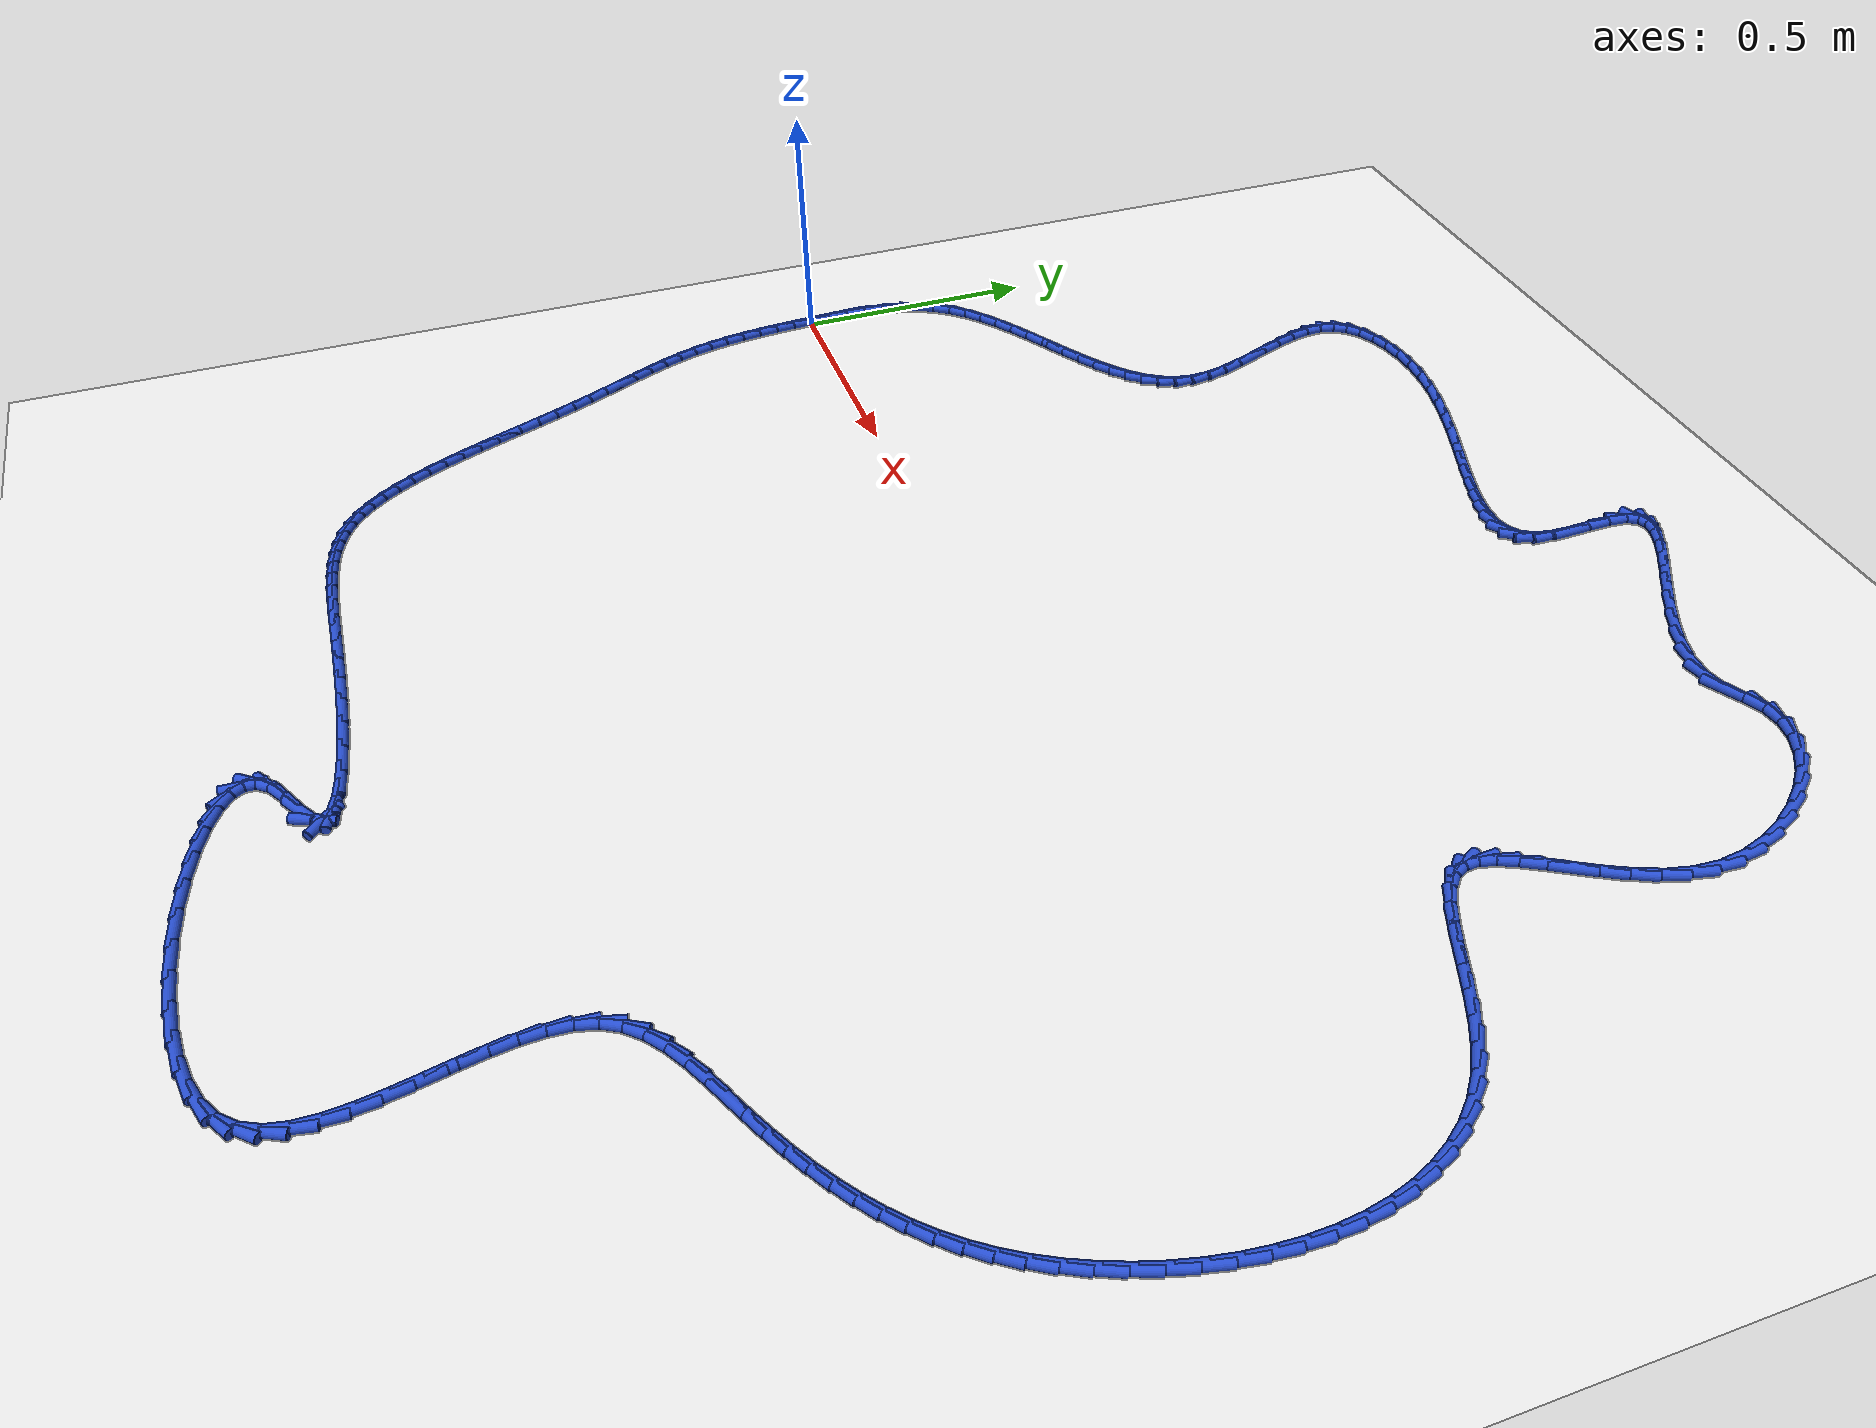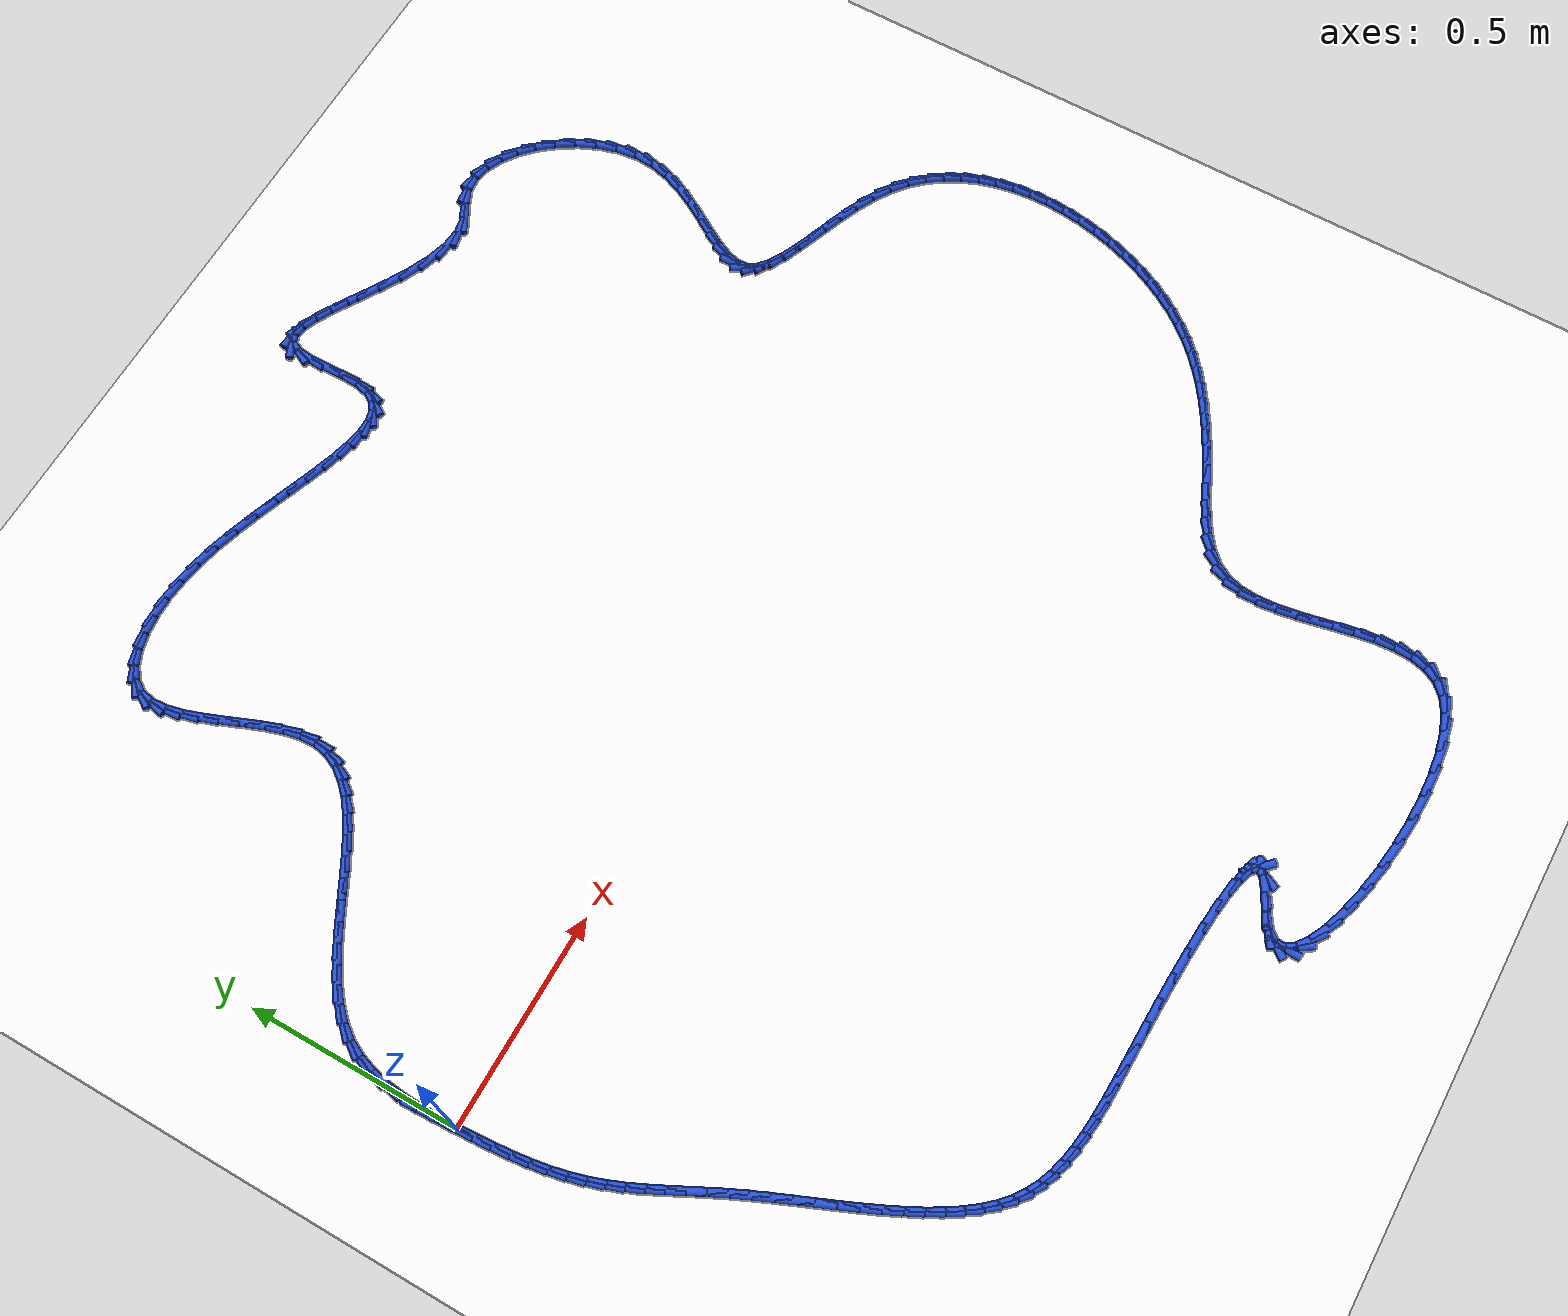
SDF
<sdf version="1.6">
 <world name="default">
  <light name="sun" type="directional">
   <pose>0 0 10 0 -0 0</pose>
   <diffuse>0.8 0.8 0.8 1</diffuse>
   <specular>0.2 0.2 0.2 1</specular>
   <attenuation>
    <range>1000</range>
    <constant>0.9</constant>
    <linear>0.01</linear>
    <quadratic>0.001</quadratic>
   </attenuation>
   <direction>-0.5 0.1 -0.9</direction>
  </light>
  <model name="ground_plane">
   <static>1</static>
   <link name="link">
    <collision name="collision">
     <geometry><plane><normal>0 0 1</normal><size>100 100</size></plane></geometry>
     <surface><friction><ode><mu>100</mu><mu2>50</mu2></ode></friction></surface>
    </collision>
    <visual name="visual">
     <cast_shadows>0</cast_shadows>
     <geometry><plane><normal>0 0 1</normal><size>100 100</size></plane></geometry>
     <material>
      <script><uri>file://media/materials/scripts/gazebo.material</uri><name>Gazebo/WhiteGlow</name></script>
     </material>
    </visual>
   </link>
  </model>
  <gravity>0 0 -9.8</gravity>
  <magnetic_field>6e-06 2.3e-05 -4.2e-05</magnetic_field>
  <atmosphere type="adiabatic"/>
  <physics name="default_physics" default="0" type="ode">
   <max_step_size>0.001</max_step_size>
   <real_time_factor>1</real_time_factor>
   <real_time_update_rate>1000</real_time_update_rate>
  </physics>
  <scene><ambient>0.4 0.4 0.4 1</ambient><background>0.7 0.7 0.7 1</background><shadows>1</shadows></scene>
  <spherical_coordinates>
   <surface_model>EARTH_WGS84</surface_model>
   <latitude_deg>0</latitude_deg>
   <longitude_deg>0</longitude_deg>
   <elevation>0</elevation>
   <heading_deg>0</heading_deg>
  </spherical_coordinates>
  <model name="line">
   <link name="link_0">
    <pose>6.288372600415926e-18 2.7755575615628914e-17 0.01 0 1.57 -1.526758649857964</pose>
    <collision name="collision">
     <geometry><cylinder><radius>0.01</radius><length>0.08</length></cylinder></geometry>
    </collision>
    <visual name="visual">
     <material>
      <script><name>Gazebo/Blue</name><uri>file://media/materials/scripts/gazebo.material</uri></script>
     </material>
     <geometry><cylinder><radius>0.01</radius><length>0.08</length></cylinder></geometry>
    </visual>
   </link>
   <link name="link_1">
    <pose>-0.0018820388010166997 0.042709383220019805 0.01 0 1.57 -1.5539022195471113</pose>
    <collision name="collision">
     <geometry><cylinder><radius>0.01</radius><length>0.08</length></cylinder></geometry>
    </collision>
    <visual name="visual">
     <material>
      <script><name>Gazebo/Blue</name><uri>file://media/materials/scripts/gazebo.material</uri></script>
     </material>
     <geometry><cylinder><radius>0.01</radius><length>0.08</length></cylinder></geometry>
    </visual>
   </link>
   <link name="link_2">
    <pose>-0.002604133918922305 0.08544774210924796 0.01 0 1.57 1.540635846049451</pose>
    <collision name="collision">
     <geometry><cylinder><radius>0.01</radius><length>0.08</length></cylinder></geometry>
    </collision>
    <visual name="visual">
     <material>
      <script><name>Gazebo/Blue</name><uri>file://media/materials/scripts/gazebo.material</uri></script>
     </material>
     <geometry><cylinder><radius>0.01</radius><length>0.08</length></cylinder></geometry>
    </visual>
   </link>
   <link name="link_3">
    <pose>-0.0013292770291949206 0.1277040415770393 0.01 0 1.57 1.4715476780531809</pose>
    <collision name="collision">
     <geometry><cylinder><radius>0.01</radius><length>0.08</length></cylinder></geometry>
    </collision>
    <visual name="visual">
     <material>
      <script><name>Gazebo/Blue</name><uri>file://media/materials/scripts/gazebo.material</uri></script>
     </material>
     <geometry><cylinder><radius>0.01</radius><length>0.08</length></cylinder></geometry>
    </visual>
   </link>
   <link name="link_4">
    <pose>0.002779540192687339 0.16896724653274864 0.01 0 1.57 1.377564583050913</pose>
    <collision name="collision">
     <geometry><cylinder><radius>0.01</radius><length>0.08</length></cylinder></geometry>
    </collision>
    <visual name="visual">
     <material>
      <script><name>Gazebo/Blue</name><uri>file://media/materials/scripts/gazebo.material</uri></script>
     </material>
     <geometry><cylinder><radius>0.01</radius><length>0.08</length></cylinder></geometry>
    </visual>
   </link>
   <link name="link_5">
    <pose>0.010559326071246366 0.20872632188573073 0.01 0 1.57 1.2560614764792688</pose>
    <collision name="collision">
     <geometry><cylinder><radius>0.01</radius><length>0.08</length></cylinder></geometry>
    </collision>
    <visual name="visual">
     <material>
      <script><name>Gazebo/Blue</name><uri>file://media/materials/scripts/gazebo.material</uri></script>
     </material>
     <geometry><cylinder><radius>0.01</radius><length>0.08</length></cylinder></geometry>
    </visual>
   </link>
   <link name="link_6">
    <pose>0.022847088931004032 0.24647023254534045 0.01 0 1.57 1.1066061216356813</pose>
    <collision name="collision">
     <geometry><cylinder><radius>0.01</radius><length>0.08</length></cylinder></geometry>
    </collision>
    <visual name="visual">
     <material>
      <script><name>Gazebo/Blue</name><uri>file://media/materials/scripts/gazebo.material</uri></script>
     </material>
     <geometry><cylinder><radius>0.01</radius><length>0.08</length></cylinder></geometry>
    </visual>
   </link>
   <link name="link_7">
    <pose>0.040479837096482243 0.28168794342093245 0.01 0 1.57 0.9417796551673666</pose>
    <collision name="collision">
     <geometry><cylinder><radius>0.01</radius><length>0.08</length></cylinder></geometry>
    </collision>
    <visual name="visual">
     <material>
      <script><name>Gazebo/Blue</name><uri>file://media/materials/scripts/gazebo.material</uri></script>
     </material>
     <geometry><cylinder><radius>0.01</radius><length>0.08</length></cylinder></geometry>
    </visual>
   </link>
   <link name="link_8">
    <pose>0.06400437496463998 0.31401920119887294 0.01 0 1.57 0.80065426163367</pose>
    <collision name="collision">
     <geometry><cylinder><radius>0.01</radius><length>0.08</length></cylinder></geometry>
    </collision>
    <visual name="visual">
     <material>
      <script><name>Gazebo/Blue</name><uri>file://media/materials/scripts/gazebo.material</uri></script>
     </material>
     <geometry><cylinder><radius>0.01</radius><length>0.08</length></cylinder></geometry>
    </visual>
   </link>
   <link name="link_9">
    <pose>0.09280208311702653 0.34370927391506456 0.01 0 1.57 0.6914011478016168</pose>
    <collision name="collision">
     <geometry><cylinder><radius>0.01</radius><length>0.08</length></cylinder></geometry>
    </collision>
    <visual name="visual">
     <material>
      <script><name>Gazebo/Blue</name><uri>file://media/materials/scripts/gazebo.material</uri></script>
     </material>
     <geometry><cylinder><radius>0.01</radius><length>0.08</length></cylinder></geometry>
    </visual>
   </link>
   <link name="link_10">
    <pose>0.12596182958552965 0.3711554108773606 0.01 0 1.57 0.6102123697754932</pose>
    <collision name="collision">
     <geometry><cylinder><radius>0.01</radius><length>0.08</length></cylinder></geometry>
    </collision>
    <visual name="visual">
     <material>
      <script><name>Gazebo/Blue</name><uri>file://media/materials/scripts/gazebo.material</uri></script>
     </material>
     <geometry><cylinder><radius>0.01</radius><length>0.08</length></cylinder></geometry>
    </visual>
   </link>
   <link name="link_11">
    <pose>0.16257248240136604 0.39675486139396315 0.01 0 1.57 0.5527185018217031</pose>
    <collision name="collision">
     <geometry><cylinder><radius>0.01</radius><length>0.08</length></cylinder></geometry>
    </collision>
    <visual name="visual">
     <material>
      <script><name>Gazebo/Blue</name><uri>file://media/materials/scripts/gazebo.material</uri></script>
     </material>
     <geometry><cylinder><radius>0.01</radius><length>0.08</length></cylinder></geometry>
    </visual>
   </link>
   <link name="link_12">
    <pose>0.2017229095957525 0.42090487477307403 0.01 0 1.57 0.5153575408454867</pose>
    <collision name="collision">
     <geometry><cylinder><radius>0.01</radius><length>0.08</length></cylinder></geometry>
    </collision>
    <visual name="visual">
     <material>
      <script><name>Gazebo/Blue</name><uri>file://media/materials/scripts/gazebo.material</uri></script>
     </material>
     <geometry><cylinder><radius>0.01</radius><length>0.08</length></cylinder></geometry>
    </visual>
   </link>
   <link name="link_13">
    <pose>0.24250197919990554 0.44400270032289524 0.01 0 1.57 0.4957810918882343</pose>
    <collision name="collision">
     <geometry><cylinder><radius>0.01</radius><length>0.08</length></cylinder></geometry>
    </collision>
    <visual name="visual">
     <material>
      <script><name>Gazebo/Blue</name><uri>file://media/materials/scripts/gazebo.material</uri></script>
     </material>
     <geometry><cylinder><radius>0.01</radius><length>0.08</length></cylinder></geometry>
    </visual>
   </link>
   <link name="link_14">
    <pose>0.283998559245042 0.4664455873516287 0.01 0 1.57 0.4929111726390121</pose>
    <collision name="collision">
     <geometry><cylinder><radius>0.01</radius><length>0.08</length></cylinder></geometry>
    </collision>
    <visual name="visual">
     <material>
      <script><name>Gazebo/Blue</name><uri>file://media/materials/scripts/gazebo.material</uri></script>
     </material>
     <geometry><cylinder><radius>0.01</radius><length>0.08</length></cylinder></geometry>
    </visual>
   </link>
   <link name="link_15">
    <pose>0.3253015177623788 0.48863078516747666 0.01 0 1.57 0.5069544342552839</pose>
    <collision name="collision">
     <geometry><cylinder><radius>0.01</radius><length>0.08</length></cylinder></geometry>
    </collision>
    <visual name="visual">
     <material>
      <script><name>Gazebo/Blue</name><uri>file://media/materials/scripts/gazebo.material</uri></script>
     </material>
     <geometry><cylinder><radius>0.01</radius><length>0.08</length></cylinder></geometry>
    </visual>
   </link>
   <link name="link_16">
    <pose>0.3654997227831325 0.5109555430786408 0.01 0 1.57 0.5394980149726251</pose>
    <collision name="collision">
     <geometry><cylinder><radius>0.01</radius><length>0.08</length></cylinder></geometry>
    </collision>
    <visual name="visual">
     <material>
      <script><name>Gazebo/Blue</name><uri>file://media/materials/scripts/gazebo.material</uri></script>
     </material>
     <geometry><cylinder><radius>0.01</radius><length>0.08</length></cylinder></geometry>
    </visual>
   </link>
   <link name="link_17">
    <pose>0.40368204233851956 0.533817110393323 0.01 0 1.57 0.5937164828958916</pose>
    <collision name="collision">
     <geometry><cylinder><radius>0.01</radius><length>0.08</length></cylinder></geometry>
    </collision>
    <visual name="visual">
     <material>
      <script><name>Gazebo/Blue</name><uri>file://media/materials/scripts/gazebo.material</uri></script>
     </material>
     <geometry><cylinder><radius>0.01</radius><length>0.08</length></cylinder></geometry>
    </visual>
   </link>
   <link name="link_18">
    <pose>0.4389373444597569 0.5576127364197254 0.01 0 1.57 0.6746091817504541</pose>
    <collision name="collision">
     <geometry><cylinder><radius>0.01</radius><length>0.08</length></cylinder></geometry>
    </collision>
    <visual name="visual">
     <material>
      <script><name>Gazebo/Blue</name><uri>file://media/materials/scripts/gazebo.material</uri></script>
     </material>
     <geometry><cylinder><radius>0.01</radius><length>0.08</length></cylinder></geometry>
    </visual>
   </link>
   <link name="link_19">
    <pose>0.4703544971780613 0.5827396704660501 0.01 0 1.57 0.7889035346942662</pose>
    <collision name="collision">
     <geometry><cylinder><radius>0.01</radius><length>0.08</length></cylinder></geometry>
    </collision>
    <visual name="visual">
     <material>
      <script><name>Gazebo/Blue</name><uri>file://media/materials/scripts/gazebo.material</uri></script>
     </material>
     <geometry><cylinder><radius>0.01</radius><length>0.08</length></cylinder></geometry>
    </visual>
   </link>
   <link name="link_20">
    <pose>0.4970223685246496 0.6095951618404989 0.01 0 1.57 0.9435782249534778</pose>
    <collision name="collision">
     <geometry><cylinder><radius>0.01</radius><length>0.08</length></cylinder></geometry>
    </collision>
    <visual name="visual">
     <material>
      <script><name>Gazebo/Blue</name><uri>file://media/materials/scripts/gazebo.material</uri></script>
     </material>
     <geometry><cylinder><radius>0.01</radius><length>0.08</length></cylinder></geometry>
    </visual>
   </link>
   <link name="link_21">
    <pose>0.518029826530738 0.6385764598512735 0.01 0 1.57 1.1411280348317558</pose>
    <collision name="collision">
     <geometry><cylinder><radius>0.01</radius><length>0.08</length></cylinder></geometry>
    </collision>
    <visual name="visual">
     <material>
      <script><name>Gazebo/Blue</name><uri>file://media/materials/scripts/gazebo.material</uri></script>
     </material>
     <geometry><cylinder><radius>0.01</radius><length>0.08</length></cylinder></geometry>
    </visual>
   </link>
   <link name="link_22">
    <pose>0.5324657392275438 0.6700808138065765 0.01 0 1.57 1.3714936634912922</pose>
    <collision name="collision">
     <geometry><cylinder><radius>0.01</radius><length>0.08</length></cylinder></geometry>
    </collision>
    <visual name="visual">
     <material>
      <script><name>Gazebo/Blue</name><uri>file://media/materials/scripts/gazebo.material</uri></script>
     </material>
     <geometry><cylinder><radius>0.01</radius><length>0.08</length></cylinder></geometry>
    </visual>
   </link>
   <link name="link_23">
    <pose>0.5394189746462833 0.7045054730146092 0.01 0 1.57 -1.5384329638940883</pose>
    <collision name="collision">
     <geometry><cylinder><radius>0.01</radius><length>0.08</length></cylinder></geometry>
    </collision>
    <visual name="visual">
     <material>
      <script><name>Gazebo/Blue</name><uri>file://media/materials/scripts/gazebo.material</uri></script>
     </material>
     <geometry><cylinder><radius>0.01</radius><length>0.08</length></cylinder></geometry>
    </visual>
   </link>
   <link name="link_24">
    <pose>0.5382001902299707 0.7421517113626651 0.01 0 1.57 -1.3685313954959126</pose>
    <collision name="collision">
     <geometry><cylinder><radius>0.01</radius><length>0.08</length></cylinder></geometry>
    </collision>
    <visual name="visual">
     <material>
      <script><name>Gazebo/Blue</name><uri>file://media/materials/scripts/gazebo.material</uri></script>
     </material>
     <geometry><cylinder><radius>0.01</radius><length>0.08</length></cylinder></geometry>
    </visual>
   </link>
   <link name="link_25">
    <pose>0.529917156613375 0.7825431339863955 0.01 0 1.57 -1.2645890546343348</pose>
    <collision name="collision">
     <geometry><cylinder><radius>0.01</radius><length>0.08</length></cylinder></geometry>
    </collision>
    <visual name="visual">
     <material>
      <script><name>Gazebo/Blue</name><uri>file://media/materials/scripts/gazebo.material</uri></script>
     </material>
     <geometry><cylinder><radius>0.01</radius><length>0.08</length></cylinder></geometry>
    </visual>
   </link>
   <link name="link_26">
    <pose>0.5165493606276207 0.8248261263508623 0.01 0 1.57 -1.207522079708169</pose>
    <collision name="collision">
     <geometry><cylinder><radius>0.01</radius><length>0.08</length></cylinder></geometry>
    </collision>
    <visual name="visual">
     <material>
      <script><name>Gazebo/Blue</name><uri>file://media/materials/scripts/gazebo.material</uri></script>
     </material>
     <geometry><cylinder><radius>0.01</radius><length>0.08</length></cylinder></geometry>
    </visual>
   </link>
   <link name="link_27">
    <pose>0.5000820379705058 0.8681445862013843 0.01 0 1.57 -1.186678607799389</pose>
    <collision name="collision">
     <geometry><cylinder><radius>0.01</radius><length>0.08</length></cylinder></geometry>
    </collision>
    <visual name="visual">
     <material>
      <script><name>Gazebo/Blue</name><uri>file://media/materials/scripts/gazebo.material</uri></script>
     </material>
     <geometry><cylinder><radius>0.01</radius><length>0.08</length></cylinder></geometry>
    </visual>
   </link>
   <link name="link_28">
    <pose>0.4825004243398282 0.9116424112832785 0.01 0 1.57 -1.1987285599157842</pose>
    <collision name="collision">
     <geometry><cylinder><radius>0.01</radius><length>0.08</length></cylinder></geometry>
    </collision>
    <visual name="visual">
     <material>
      <script><name>Gazebo/Blue</name><uri>file://media/materials/scripts/gazebo.material</uri></script>
     </material>
     <geometry><cylinder><radius>0.01</radius><length>0.08</length></cylinder></geometry>
    </visual>
   </link>
   <link name="link_29">
    <pose>0.46578975543338624 0.9544634993418641 0.01 0 1.57 -1.2470473855598898</pose>
    <collision name="collision">
     <geometry><cylinder><radius>0.01</radius><length>0.08</length></cylinder></geometry>
    </collision>
    <visual name="visual">
     <material>
      <script><name>Gazebo/Blue</name><uri>file://media/materials/scripts/gazebo.material</uri></script>
     </material>
     <geometry><cylinder><radius>0.01</radius><length>0.08</length></cylinder></geometry>
    </visual>
   </link>
   <link name="link_30">
    <pose>0.4519352669489779 0.9957517481224589 0.01 0 1.57 -1.3431114413769207</pose>
    <collision name="collision">
     <geometry><cylinder><radius>0.01</radius><length>0.08</length></cylinder></geometry>
    </collision>
    <visual name="visual">
     <material>
      <script><name>Gazebo/Blue</name><uri>file://media/materials/scripts/gazebo.material</uri></script>
     </material>
     <geometry><cylinder><radius>0.01</radius><length>0.08</length></cylinder></geometry>
    </visual>
   </link>
   <link name="link_31">
    <pose>0.44292219458440146 1.034651055370381 0.01 0 1.57 -1.5095501859078324</pose>
    <collision name="collision">
     <geometry><cylinder><radius>0.01</radius><length>0.08</length></cylinder></geometry>
    </collision>
    <visual name="visual">
     <material>
      <script><name>Gazebo/Blue</name><uri>file://media/materials/scripts/gazebo.material</uri></script>
     </material>
     <geometry><cylinder><radius>0.01</radius><length>0.08</length></cylinder></geometry>
    </visual>
   </link>
   <link name="link_32">
    <pose>0.440735774037455 1.0703053188309484 0.01 0 1.57 1.3638250067765472</pose>
    <collision name="collision">
     <geometry><cylinder><radius>0.01</radius><length>0.08</length></cylinder></geometry>
    </collision>
    <visual name="visual">
     <material>
      <script><name>Gazebo/Blue</name><uri>file://media/materials/scripts/gazebo.material</uri></script>
     </material>
     <geometry><cylinder><radius>0.01</radius><length>0.08</length></cylinder></geometry>
    </visual>
   </link>
   <link name="link_33">
    <pose>0.4473612410059365 1.101858436249479 0.01 0 1.57 1.0010813951349533</pose>
    <collision name="collision">
     <geometry><cylinder><radius>0.01</radius><length>0.08</length></cylinder></geometry>
    </collision>
    <visual name="visual">
     <material>
      <script><name>Gazebo/Blue</name><uri>file://media/materials/scripts/gazebo.material</uri></script>
     </material>
     <geometry><cylinder><radius>0.01</radius><length>0.08</length></cylinder></geometry>
    </visual>
   </link>
   <link name="link_34">
    <pose>0.4644480901876743 1.1285330294487175 0.01 0 1.57 0.6746042730657024</pose>
    <collision name="collision">
     <geometry><cylinder><radius>0.01</radius><length>0.08</length></cylinder></geometry>
    </collision>
    <visual name="visual">
     <material>
      <script><name>Gazebo/Blue</name><uri>file://media/materials/scripts/gazebo.material</uri></script>
     </material>
     <geometry><cylinder><radius>0.01</radius><length>0.08</length></cylinder></geometry>
    </visual>
   </link>
   <link name="link_35">
    <pose>0.4913901369211278 1.150080628774802 0.01 0 1.57 0.43509686882973314</pose>
    <collision name="collision">
     <geometry><cylinder><radius>0.01</radius><length>0.08</length></cylinder></geometry>
    </collision>
    <visual name="visual">
     <material>
      <script><name>Gazebo/Blue</name><uri>file://media/materials/scripts/gazebo.material</uri></script>
     </material>
     <geometry><cylinder><radius>0.01</radius><length>0.08</length></cylinder></geometry>
    </visual>
   </link>
   <link name="link_36">
    <pose>0.5266522029936462 1.166470593675032 0.01 0 1.57 0.2603942609655746</pose>
    <collision name="collision">
     <geometry><cylinder><radius>0.01</radius><length>0.08</length></cylinder></geometry>
    </collision>
    <visual name="visual">
     <material>
      <script><name>Gazebo/Blue</name><uri>file://media/materials/scripts/gazebo.material</uri></script>
     </material>
     <geometry><cylinder><radius>0.01</radius><length>0.08</length></cylinder></geometry>
    </visual>
   </link>
   <link name="link_37">
    <pose>0.5686962242809466 1.1776729602812057 0.01 0 1.57 0.1258916611867134</pose>
    <collision name="collision">
     <geometry><cylinder><radius>0.01</radius><length>0.08</length></cylinder></geometry>
    </collision>
    <visual name="visual">
     <material>
      <script><name>Gazebo/Blue</name><uri>file://media/materials/scripts/gazebo.material</uri></script>
     </material>
     <geometry><cylinder><radius>0.01</radius><length>0.08</length></cylinder></geometry>
    </visual>
   </link>
   <link name="link_38">
    <pose>0.6159841366587461 1.1836577647251227 0.01 0 1.57 0.0144572070186565</pose>
    <collision name="collision">
     <geometry><cylinder><radius>0.01</radius><length>0.08</length></cylinder></geometry>
    </collision>
    <visual name="visual">
     <material>
      <script><name>Gazebo/Blue</name><uri>file://media/materials/scripts/gazebo.material</uri></script>
     </material>
     <geometry><cylinder><radius>0.01</radius><length>0.08</length></cylinder></geometry>
    </visual>
   </link>
   <link name="link_39">
    <pose>0.6669778760027624 1.1843950431385826 0.01 0 1.57 -0.08510780798336802</pose>
    <collision name="collision">
     <geometry><cylinder><radius>0.01</radius><length>0.08</length></cylinder></geometry>
    </collision>
    <visual name="visual">
     <material>
      <script><name>Gazebo/Blue</name><uri>file://media/materials/scripts/gazebo.material</uri></script>
     </material>
     <geometry><cylinder><radius>0.01</radius><length>0.08</length></cylinder></geometry>
    </visual>
   </link>
   <link name="link_40">
    <pose>0.7201433205949859 1.1798592920694408 0.01 0 1.57 -0.1729592587069869</pose>
    <collision name="collision">
     <geometry><cylinder><radius>0.01</radius><length>0.08</length></cylinder></geometry>
    </collision>
    <visual name="visual">
     <material>
      <script><name>Gazebo/Blue</name><uri>file://media/materials/scripts/gazebo.material</uri></script>
     </material>
     <geometry><cylinder><radius>0.01</radius><length>0.08</length></cylinder></geometry>
    </visual>
   </link>
   <link name="link_41">
    <pose>0.7742791219289952 1.1704015057862984 0.01 0 1.57 -0.2406707334244392</pose>
    <collision name="collision">
     <geometry><cylinder><radius>0.01</radius><length>0.08</length></cylinder></geometry>
    </collision>
    <visual name="visual">
     <material>
      <script><name>Gazebo/Blue</name><uri>file://media/materials/scripts/gazebo.material</uri></script>
     </material>
     <geometry><cylinder><radius>0.01</radius><length>0.08</length></cylinder></geometry>
    </visual>
   </link>
   <link name="link_42">
    <pose>0.8287643207282968 1.1570293276346737 0.01 0 1.57 -0.2902959865952461</pose>
    <collision name="collision">
     <geometry><cylinder><radius>0.01</radius><length>0.08</length></cylinder></geometry>
    </collision>
    <visual name="visual">
     <material>
      <script><name>Gazebo/Blue</name><uri>file://media/materials/scripts/gazebo.material</uri></script>
     </material>
     <geometry><cylinder><radius>0.01</radius><length>0.08</length></cylinder></geometry>
    </visual>
   </link>
   <link name="link_43">
    <pose>0.8830362791435478 1.1408163854913769 0.01 0 1.57 -0.324239251990807</pose>
    <collision name="collision">
     <geometry><cylinder><radius>0.01</radius><length>0.08</length></cylinder></geometry>
    </collision>
    <visual name="visual">
     <material>
      <script><name>Gazebo/Blue</name><uri>file://media/materials/scripts/gazebo.material</uri></script>
     </material>
     <geometry><cylinder><radius>0.01</radius><length>0.08</length></cylinder></geometry>
    </visual>
   </link>
   <link name="link_44">
    <pose>0.9365323593254058 1.1228363072332188 0.01 0 1.57 -0.3438039437400636</pose>
    <collision name="collision">
     <geometry><cylinder><radius>0.01</radius><length>0.08</length></cylinder></geometry>
    </collision>
    <visual name="visual">
     <material>
      <script><name>Gazebo/Blue</name><uri>file://media/materials/scripts/gazebo.material</uri></script>
     </material>
     <geometry><cylinder><radius>0.01</radius><length>0.08</length></cylinder></geometry>
    </visual>
   </link>
   <link name="link_45">
    <pose>0.9886899234245279 1.10416272073701 0.01 0 1.57 -0.3490944805405868</pose>
    <collision name="collision">
     <geometry><cylinder><radius>0.01</radius><length>0.08</length></cylinder></geometry>
    </collision>
    <visual name="visual">
     <material>
      <script><name>Gazebo/Blue</name><uri>file://media/materials/scripts/gazebo.material</uri></script>
     </material>
     <geometry><cylinder><radius>0.01</radius><length>0.08</length></cylinder></geometry>
    </visual>
   </link>
   <link name="link_46">
    <pose>1.0389463335915716 1.0858692538795607 0.01 0 1.57 -0.3387666432334503</pose>
    <collision name="collision">
     <geometry><cylinder><radius>0.01</radius><length>0.08</length></cylinder></geometry>
    </collision>
    <visual name="visual">
     <material>
      <script><name>Gazebo/Blue</name><uri>file://media/materials/scripts/gazebo.material</uri></script>
     </material>
     <geometry><cylinder><radius>0.01</radius><length>0.08</length></cylinder></geometry>
    </visual>
   </link>
   <link name="link_47">
    <pose>1.0867389519771946 1.069029534537682 0.01 0 1.57 -0.309442813718152</pose>
    <collision name="collision">
     <geometry><cylinder><radius>0.01</radius><length>0.08</length></cylinder></geometry>
    </collision>
    <visual name="visual">
     <material>
      <script><name>Gazebo/Blue</name><uri>file://media/materials/scripts/gazebo.material</uri></script>
     </material>
     <geometry><cylinder><radius>0.01</radius><length>0.08</length></cylinder></geometry>
    </visual>
   </link>
   <link name="link_48">
    <pose>1.1315051407320547 1.0547171905881834 0.01 0 1.57 -0.25448837019610693</pose>
    <collision name="collision">
     <geometry><cylinder><radius>0.01</radius><length>0.08</length></cylinder></geometry>
    </collision>
    <visual name="visual">
     <material>
      <script><name>Gazebo/Blue</name><uri>file://media/materials/scripts/gazebo.material</uri></script>
     </material>
     <geometry><cylinder><radius>0.01</radius><length>0.08</length></cylinder></geometry>
    </visual>
   </link>
   <link name="link_49">
    <pose>1.1726822620068078 1.0440058499078755 0.01 0 1.57 -0.16162022216920774</pose>
    <collision name="collision">
     <geometry><cylinder><radius>0.01</radius><length>0.08</length></cylinder></geometry>
    </collision>
    <visual name="visual">
     <material>
      <script><name>Gazebo/Blue</name><uri>file://media/materials/scripts/gazebo.material</uri></script>
     </material>
     <geometry><cylinder><radius>0.01</radius><length>0.08</length></cylinder></geometry>
    </visual>
   </link>
   <link name="link_50">
    <pose>1.2097076779521128 1.0379691403735694 0.01 0 1.57 -0.008927058878610774</pose>
    <collision name="collision">
     <geometry><cylinder><radius>0.01</radius><length>0.08</length></cylinder></geometry>
    </collision>
    <visual name="visual">
     <material>
      <script><name>Gazebo/Blue</name><uri>file://media/materials/scripts/gazebo.material</uri></script>
     </material>
     <geometry><cylinder><radius>0.01</radius><length>0.08</length></cylinder></geometry>
    </visual>
   </link>
   <link name="link_51">
    <pose>1.2420187507186262 1.037680689862075 0.01 0 1.57 0.23712718297499777</pose>
    <collision name="collision">
     <geometry><cylinder><radius>0.01</radius><length>0.08</length></cylinder></geometry>
    </collision>
    <visual name="visual">
     <material>
      <script><name>Gazebo/Blue</name><uri>file://media/materials/scripts/gazebo.material</uri></script>
     </material>
     <geometry><cylinder><radius>0.01</radius><length>0.08</length></cylinder></geometry>
    </visual>
   </link>
   <link name="link_52">
    <pose>1.2690528424570062 1.0442141262502032 0.01 0 1.57 0.5977155709318069</pose>
    <collision name="collision">
     <geometry><cylinder><radius>0.01</radius><length>0.08</length></cylinder></geometry>
    </collision>
    <visual name="visual">
     <material>
      <script><name>Gazebo/Blue</name><uri>file://media/materials/scripts/gazebo.material</uri></script>
     </material>
     <geometry><cylinder><radius>0.01</radius><length>0.08</length></cylinder></geometry>
    </visual>
   </link>
   <link name="link_53">
    <pose>1.2902473153179097 1.0586430774147642 0.01 0 1.57 1.0070380241342893</pose>
    <collision name="collision">
     <geometry><cylinder><radius>0.01</radius><length>0.08</length></cylinder></geometry>
    </collision>
    <visual name="visual">
     <material>
      <script><name>Gazebo/Blue</name><uri>file://media/materials/scripts/gazebo.material</uri></script>
     </material>
     <geometry><cylinder><radius>0.01</radius><length>0.08</length></cylinder></geometry>
    </visual>
   </link>
   <link name="link_54">
    <pose>1.3050395314519943 1.0820411712325682 0.01 0 1.57 1.340478955888795</pose>
    <collision name="collision">
     <geometry><cylinder><radius>0.01</radius><length>0.08</length></cylinder></geometry>
    </collision>
    <visual name="visual">
     <material>
      <script><name>Gazebo/Blue</name><uri>file://media/materials/scripts/gazebo.material</uri></script>
     </material>
     <geometry><cylinder><radius>0.01</radius><length>0.08</length></cylinder></geometry>
    </visual>
   </link>
   <link name="link_55">
    <pose>1.3128768254789365 1.1154655810520033 0.01 0 1.57 1.5326426162205966</pose>
    <collision name="collision">
     <geometry><cylinder><radius>0.01</radius><length>0.08</length></cylinder></geometry>
    </collision>
    <visual name="visual">
     <material>
      <script><name>Gazebo/Blue</name><uri>file://media/materials/scripts/gazebo.material</uri></script>
     </material>
     <geometry><cylinder><radius>0.01</radius><length>0.08</length></cylinder></geometry>
    </visual>
   </link>
   <link name="link_56">
    <pose>1.3144946599905916 1.1578480749392313 0.01 0 1.57 -1.5421658577141115</pose>
    <collision name="collision">
     <geometry><cylinder><radius>0.01</radius><length>0.08</length></cylinder></geometry>
    </collision>
    <visual name="visual">
     <material>
      <script><name>Gazebo/Blue</name><uri>file://media/materials/scripts/gazebo.material</uri></script>
     </material>
     <geometry><cylinder><radius>0.01</radius><length>0.08</length></cylinder></geometry>
    </visual>
   </link>
   <link name="link_57">
    <pose>1.3131752894376507 1.2039182260027659 0.01 0 1.57 -1.5554471945693393</pose>
    <collision name="collision">
     <geometry><cylinder><radius>0.01</radius><length>0.08</length></cylinder></geometry>
    </collision>
    <visual name="visual">
     <material>
      <script><name>Gazebo/Blue</name><uri>file://media/materials/scripts/gazebo.material</uri></script>
     </material>
     <geometry><cylinder><radius>0.01</radius><length>0.08</length></cylinder></geometry>
    </visual>
   </link>
   <link name="link_58">
    <pose>1.312499966122735 1.2479122622583971 0.01 0 1.57 1.4729200648623804</pose>
    <collision name="collision">
     <geometry><cylinder><radius>0.01</radius><length>0.08</length></cylinder></geometry>
    </collision>
    <visual name="visual">
     <material>
      <script><name>Gazebo/Blue</name><uri>file://media/materials/scripts/gazebo.material</uri></script>
     </material>
     <geometry><cylinder><radius>0.01</radius><length>0.08</length></cylinder></geometry>
    </visual>
   </link>
   <link name="link_59">
    <pose>1.3160499423484682 1.2840664117219176 0.01 0 1.57 1.115177989552686</pose>
    <collision name="collision">
     <geometry><cylinder><radius>0.01</radius><length>0.08</length></cylinder></geometry>
    </collision>
    <visual name="visual">
     <material>
      <script><name>Gazebo/Blue</name><uri>file://media/materials/scripts/gazebo.material</uri></script>
     </material>
     <geometry><cylinder><radius>0.01</radius><length>0.08</length></cylinder></geometry>
    </visual>
   </link>
   <link name="link_60">
    <pose>1.3272408211976918 1.3069047848491755 0.01 0 1.57 0.40402020106702413</pose>
    <collision name="collision">
     <geometry><cylinder><radius>0.01</radius><length>0.08</length></cylinder></geometry>
    </collision>
    <visual name="visual">
     <material>
      <script><name>Gazebo/Blue</name><uri>file://media/materials/scripts/gazebo.material</uri></script>
     </material>
     <geometry><cylinder><radius>0.01</radius><length>0.08</length></cylinder></geometry>
    </visual>
   </link>
   <link name="link_61">
    <pose>1.3469645005195718 1.3153374494921228 0.01 0 1.57 -0.13333971773925576</pose>
    <collision name="collision">
     <geometry><cylinder><radius>0.01</radius><length>0.08</length></cylinder></geometry>
    </collision>
    <visual name="visual">
     <material>
      <script><name>Gazebo/Blue</name><uri>file://media/materials/scripts/gazebo.material</uri></script>
     </material>
     <geometry><cylinder><radius>0.01</radius><length>0.08</length></cylinder></geometry>
    </visual>
   </link>
   <link name="link_62">
    <pose>1.374146795988078 1.3116913355603654 0.01 0 1.57 -0.37797741302061216</pose>
    <collision name="collision">
     <geometry><cylinder><radius>0.01</radius><length>0.08</length></cylinder></geometry>
    </collision>
    <visual name="visual">
     <material>
      <script><name>Gazebo/Blue</name><uri>file://media/materials/scripts/gazebo.material</uri></script>
     </material>
     <geometry><cylinder><radius>0.01</radius><length>0.08</length></cylinder></geometry>
    </visual>
   </link>
   <link name="link_63">
    <pose>1.4076615827370627 1.2983836406354397 0.01 0 1.57 -0.487960572976232</pose>
    <collision name="collision">
     <geometry><cylinder><radius>0.01</radius><length>0.08</length></cylinder></geometry>
    </collision>
    <visual name="visual">
     <material>
      <script><name>Gazebo/Blue</name><uri>file://media/materials/scripts/gazebo.material</uri></script>
     </material>
     <geometry><cylinder><radius>0.01</radius><length>0.08</length></cylinder></geometry>
    </visual>
   </link>
   <link name="link_64">
    <pose>1.4463827359003765 1.2778315622988832 0.01 0 1.57 -0.535222612706178</pose>
    <collision name="collision">
     <geometry><cylinder><radius>0.01</radius><length>0.08</length></cylinder></geometry>
    </collision>
    <visual name="visual">
     <material>
      <script><name>Gazebo/Blue</name><uri>file://media/materials/scripts/gazebo.material</uri></script>
     </material>
     <geometry><cylinder><radius>0.01</radius><length>0.08</length></cylinder></geometry>
    </visual>
   </link>
   <link name="link_65">
    <pose>1.4891841306118727 1.2524522981322326 0.01 0 1.57 -0.5458006852685703</pose>
    <collision name="collision">
     <geometry><cylinder><radius>0.01</radius><length>0.08</length></cylinder></geometry>
    </collision>
    <visual name="visual">
     <material>
      <script><name>Gazebo/Blue</name><uri>file://media/materials/scripts/gazebo.material</uri></script>
     </material>
     <geometry><cylinder><radius>0.01</radius><length>0.08</length></cylinder></geometry>
    </visual>
   </link>
   <link name="link_66">
    <pose>1.5349396420054042 1.2246630457170244 0.01 0 1.57 -0.5284663540800525</pose>
    <collision name="collision">
     <geometry><cylinder><radius>0.01</radius><length>0.08</length></cylinder></geometry>
    </collision>
    <visual name="visual">
     <material>
      <script><name>Gazebo/Blue</name><uri>file://media/materials/scripts/gazebo.material</uri></script>
     </material>
     <geometry><cylinder><radius>0.01</radius><length>0.08</length></cylinder></geometry>
    </visual>
   </link>
   <link name="link_67">
    <pose>1.5825231452148214 1.1968810026347971 0.01 0 1.57 -0.48357390207894746</pose>
    <collision name="collision">
     <geometry><cylinder><radius>0.01</radius><length>0.08</length></cylinder></geometry>
    </collision>
    <visual name="visual">
     <material>
      <script><name>Gazebo/Blue</name><uri>file://media/materials/scripts/gazebo.material</uri></script>
     </material>
     <geometry><cylinder><radius>0.01</radius><length>0.08</length></cylinder></geometry>
    </visual>
   </link>
   <link name="link_68">
    <pose>1.6308085153739782 1.1715233664670863 0.01 0 1.57 -0.4049646222156277</pose>
    <collision name="collision">
     <geometry><cylinder><radius>0.01</radius><length>0.08</length></cylinder></geometry>
    </collision>
    <visual name="visual">
     <material>
      <script><name>Gazebo/Blue</name><uri>file://media/materials/scripts/gazebo.material</uri></script>
     </material>
     <geometry><cylinder><radius>0.01</radius><length>0.08</length></cylinder></geometry>
    </visual>
   </link>
   <link name="link_69">
    <pose>1.678669627616725 1.15100733479543 0.01 0 1.57 -0.2788105046080815</pose>
    <collision name="collision">
     <geometry><cylinder><radius>0.01</radius><length>0.08</length></cylinder></geometry>
    </collision>
    <visual name="visual">
     <material>
      <script><name>Gazebo/Blue</name><uri>file://media/materials/scripts/gazebo.material</uri></script>
     </material>
     <geometry><cylinder><radius>0.01</radius><length>0.08</length></cylinder></geometry>
    </visual>
   </link>
   <link name="link_70">
    <pose>1.724980357076915 1.137750105201364 0.01 0 1.57 -0.08189033585099399</pose>
    <collision name="collision">
     <geometry><cylinder><radius>0.01</radius><length>0.08</length></cylinder></geometry>
    </collision>
    <visual name="visual">
     <material>
      <script><name>Gazebo/Blue</name><uri>file://media/materials/scripts/gazebo.material</uri></script>
     </material>
     <geometry><cylinder><radius>0.01</radius><length>0.08</length></cylinder></geometry>
    </visual>
   </link>
   <link name="link_71">
    <pose>1.7686145788883993 1.1341688752664263 0.01 0 1.57 0.21053222582493344</pose>
    <collision name="collision">
     <geometry><cylinder><radius>0.01</radius><length>0.08</length></cylinder></geometry>
    </collision>
    <visual name="visual">
     <material>
      <script><name>Gazebo/Blue</name><uri>file://media/materials/scripts/gazebo.material</uri></script>
     </material>
     <geometry><cylinder><radius>0.01</radius><length>0.08</length></cylinder></geometry>
    </visual>
   </link>
   <link name="link_72">
    <pose>1.8084461681850321 1.142680842572154 0.01 0 1.57 0.5015818451993034</pose>
    <collision name="collision">
     <geometry><cylinder><radius>0.01</radius><length>0.08</length></cylinder></geometry>
    </collision>
    <visual name="visual">
     <material>
      <script><name>Gazebo/Blue</name><uri>file://media/materials/scripts/gazebo.material</uri></script>
     </material>
     <geometry><cylinder><radius>0.01</radius><length>0.08</length></cylinder></geometry>
    </visual>
   </link>
   <link name="link_73">
    <pose>1.8443363856615276 1.1623615379575905 0.01 0 1.57 0.42926095401109354</pose>
    <collision name="collision">
     <geometry><cylinder><radius>0.01</radius><length>0.08</length></cylinder></geometry>
    </collision>
    <visual name="visual">
     <material>
      <script><name>Gazebo/Blue</name><uri>file://media/materials/scripts/gazebo.material</uri></script>
     </material>
     <geometry><cylinder><radius>0.01</radius><length>0.08</length></cylinder></geometry>
    </visual>
   </link>
   <link name="link_74">
    <pose>1.8801407262592675 1.1787501454397649 0.01 0 1.57 0.10622360502540779</pose>
    <collision name="collision">
     <geometry><cylinder><radius>0.01</radius><length>0.08</length></cylinder></geometry>
    </collision>
    <visual name="visual">
     <material>
      <script><name>Gazebo/Blue</name><uri>file://media/materials/scripts/gazebo.material</uri></script>
     </material>
     <geometry><cylinder><radius>0.01</radius><length>0.08</length></cylinder></geometry>
    </visual>
   </link>
   <link name="link_75">
    <pose>1.9179684924167302 1.1827835287200614 0.01 0 1.57 -0.18916336632344954</pose>
    <collision name="collision">
     <geometry><cylinder><radius>0.01</radius><length>0.08</length></cylinder></geometry>
    </collision>
    <visual name="visual">
     <material>
      <script><name>Gazebo/Blue</name><uri>file://media/materials/scripts/gazebo.material</uri></script>
     </material>
     <geometry><cylinder><radius>0.01</radius><length>0.08</length></cylinder></geometry>
    </visual>
   </link>
   <link name="link_76">
    <pose>1.956822713001509 1.1753447949877114 0.01 0 1.57 -0.42472524529714856</pose>
    <collision name="collision">
     <geometry><cylinder><radius>0.01</radius><length>0.08</length></cylinder></geometry>
    </collision>
    <visual name="visual">
     <material>
      <script><name>Gazebo/Blue</name><uri>file://media/materials/scripts/gazebo.material</uri></script>
     </material>
     <geometry><cylinder><radius>0.01</radius><length>0.08</length></cylinder></geometry>
    </visual>
   </link>
   <link name="link_77">
    <pose>1.9955454905769652 1.1578323351704387 0.01 0 1.57 -0.6104460209559734</pose>
    <collision name="collision">
     <geometry><cylinder><radius>0.01</radius><length>0.08</length></cylinder></geometry>
    </collision>
    <visual name="visual">
     <material>
      <script><name>Gazebo/Blue</name><uri>file://media/materials/scripts/gazebo.material</uri></script>
     </material>
     <geometry><cylinder><radius>0.01</radius><length>0.08</length></cylinder></geometry>
    </visual>
   </link>
   <link name="link_78">
    <pose>2.032978927706464 1.131644540195969 0.01 0 1.57 -0.7631748075532377</pose>
    <collision name="collision">
     <geometry><cylinder><radius>0.01</radius><length>0.08</length></cylinder></geometry>
    </collision>
    <visual name="visual">
     <material>
      <script><name>Gazebo/Blue</name><uri>file://media/materials/scripts/gazebo.material</uri></script>
     </material>
     <geometry><cylinder><radius>0.01</radius><length>0.08</length></cylinder></geometry>
    </visual>
   </link>
   <link name="link_79">
    <pose>2.067965126953366 1.0981798009920276 0.01 0 1.57 -0.8975072496808627</pose>
    <collision name="collision">
     <geometry><cylinder><radius>0.01</radius><length>0.08</length></cylinder></geometry>
    </collision>
    <visual name="visual">
     <material>
      <script><name>Gazebo/Blue</name><uri>file://media/materials/scripts/gazebo.material</uri></script>
     </material>
     <geometry><cylinder><radius>0.01</radius><length>0.08</length></cylinder></geometry>
    </visual>
   </link>
   <link name="link_80">
    <pose>2.099346190881036 1.0588365084863385 0.01 0 1.57 -1.024958998781677</pose>
    <collision name="collision">
     <geometry><cylinder><radius>0.01</radius><length>0.08</length></cylinder></geometry>
    </collision>
    <visual name="visual">
     <material>
      <script><name>Gazebo/Blue</name><uri>file://media/materials/scripts/gazebo.material</uri></script>
     </material>
     <geometry><cylinder><radius>0.01</radius><length>0.08</length></cylinder></geometry>
    </visual>
   </link>
   <link name="link_81">
    <pose>2.1259642220528363 1.0150130536066277 0.01 0 1.57 -1.1552396517040884</pose>
    <collision name="collision">
     <geometry><cylinder><radius>0.01</radius><length>0.08</length></cylinder></geometry>
    </collision>
    <visual name="visual">
     <material>
      <script><name>Gazebo/Blue</name><uri>file://media/materials/scripts/gazebo.material</uri></script>
     </material>
     <geometry><cylinder><radius>0.01</radius><length>0.08</length></cylinder></geometry>
    </visual>
   </link>
   <link name="link_82">
    <pose>2.146661323032129 0.9681078272806198 0.01 0 1.57 -1.2975306964069067</pose>
    <collision name="collision">
     <geometry><cylinder><radius>0.01</radius><length>0.08</length></cylinder></geometry>
    </collision>
    <visual name="visual">
     <material>
      <script><name>Gazebo/Blue</name><uri>file://media/materials/scripts/gazebo.material</uri></script>
     </material>
     <geometry><cylinder><radius>0.01</radius><length>0.08</length></cylinder></geometry>
    </visual>
   </link>
   <link name="link_83">
    <pose>2.1602795963822787 0.9195192204360397 0.01 0 1.57 -1.4611265682615995</pose>
    <collision name="collision">
     <geometry><cylinder><radius>0.01</radius><length>0.08</length></cylinder></geometry>
    </collision>
    <visual name="visual">
     <material>
      <script><name>Gazebo/Blue</name><uri>file://media/materials/scripts/gazebo.material</uri></script>
     </material>
     <geometry><cylinder><radius>0.01</radius><length>0.08</length></cylinder></geometry>
    </visual>
   </link>
   <link name="link_84">
    <pose>2.1656611446666476 0.8706456240006132 0.01 0 1.57 1.4909112903726147</pose>
    <collision name="collision">
     <geometry><cylinder><radius>0.01</radius><length>0.08</length></cylinder></geometry>
    </collision>
    <visual name="visual">
     <material>
      <script><name>Gazebo/Blue</name><uri>file://media/materials/scripts/gazebo.material</uri></script>
     </material>
     <geometry><cylinder><radius>0.01</radius><length>0.08</length></cylinder></geometry>
    </visual>
   </link>
   <link name="link_85">
    <pose>2.161832407818594 0.8228195349266856 0.01 0 1.57 1.3156269300876033</pose>
    <collision name="collision">
     <geometry><cylinder><radius>0.01</radius><length>0.08</length></cylinder></geometry>
    </collision>
    <visual name="visual">
     <material>
      <script><name>Gazebo/Blue</name><uri>file://media/materials/scripts/gazebo.material</uri></script>
     </material>
     <geometry><cylinder><radius>0.01</radius><length>0.08</length></cylinder></geometry>
    </visual>
   </link>
   <link name="link_86">
    <pose>2.149793499908995 0.7766679326959685 0.01 0 1.57 1.1836804331267596</pose>
    <collision name="collision">
     <geometry><cylinder><radius>0.01</radius><length>0.08</length></cylinder></geometry>
    </collision>
    <visual name="visual">
     <material>
      <script><name>Gazebo/Blue</name><uri>file://media/materials/scripts/gazebo.material</uri></script>
     </material>
     <geometry><cylinder><radius>0.01</radius><length>0.08</length></cylinder></geometry>
    </visual>
   </link>
   <link name="link_87">
    <pose>2.1317418584526027 0.732389796751261 0.01 0 1.57 1.0931426278462735</pose>
    <collision name="collision">
     <geometry><cylinder><radius>0.01</radius><length>0.08</length></cylinder></geometry>
    </collision>
    <visual name="visual">
     <material>
      <script><name>Gazebo/Blue</name><uri>file://media/materials/scripts/gazebo.material</uri></script>
     </material>
     <geometry><cylinder><radius>0.01</radius><length>0.08</length></cylinder></geometry>
    </visual>
   </link>
   <link name="link_88">
    <pose>2.1098917232688565 0.6901781003161623 0.01 0 1.57 1.0403182158706692</pose>
    <collision name="collision">
     <geometry><cylinder><radius>0.01</radius><length>0.08</length></cylinder></geometry>
    </collision>
    <visual name="visual">
     <material>
      <script><name>Gazebo/Blue</name><uri>file://media/materials/scripts/gazebo.material</uri></script>
     </material>
     <geometry><cylinder><radius>0.01</radius><length>0.08</length></cylinder></geometry>
    </visual>
   </link>
   <link name="link_89">
    <pose>2.0864573341771933 0.6502258166142688 0.01 0 1.57 1.024428295170089</pose>
    <collision name="collision">
     <geometry><cylinder><radius>0.01</radius><length>0.08</length></cylinder></geometry>
    </collision>
    <visual name="visual">
     <material>
      <script><name>Gazebo/Blue</name><uri>file://media/materials/scripts/gazebo.material</uri></script>
     </material>
     <geometry><cylinder><radius>0.01</radius><length>0.08</length></cylinder></geometry>
    </visual>
   </link>
   <link name="link_90">
    <pose>2.0636529309970535 0.612725918869179 0.01 0 1.57 1.050714243565556</pose>
    <collision name="collision">
     <geometry><cylinder><radius>0.01</radius><length>0.08</length></cylinder></geometry>
    </collision>
    <visual name="visual">
     <material>
      <script><name>Gazebo/Blue</name><uri>file://media/materials/scripts/gazebo.material</uri></script>
     </material>
     <geometry><cylinder><radius>0.01</radius><length>0.08</length></cylinder></geometry>
    </visual>
   </link>
   <link name="link_91">
    <pose>2.0436927535478753 0.5778713803044897 0.01 0 1.57 1.1351746572585304</pose>
    <collision name="collision">
     <geometry><cylinder><radius>0.01</radius><length>0.08</length></cylinder></geometry>
    </collision>
    <visual name="visual">
     <material>
      <script><name>Gazebo/Blue</name><uri>file://media/materials/scripts/gazebo.material</uri></script>
     </material>
     <geometry><cylinder><radius>0.01</radius><length>0.08</length></cylinder></geometry>
    </visual>
   </link>
   <link name="link_92">
    <pose>2.028791041649098 0.5458551741437997 0.01 0 1.57 1.3134274033391198</pose>
    <collision name="collision">
     <geometry><cylinder><radius>0.01</radius><length>0.08</length></cylinder></geometry>
    </collision>
    <visual name="visual">
     <material>
      <script><name>Gazebo/Blue</name><uri>file://media/materials/scripts/gazebo.material</uri></script>
     </material>
     <geometry><cylinder><radius>0.01</radius><length>0.08</length></cylinder></geometry>
    </visual>
   </link>
   <link name="link_93">
    <pose>2.02116203512016 0.5168702736107054 0.01 0 1.57 -1.4988462729532606</pose>
    <collision name="collision">
     <geometry><cylinder><radius>0.01</radius><length>0.08</length></cylinder></geometry>
    </collision>
    <visual name="visual">
     <material>
      <script><name>Gazebo/Blue</name><uri>file://media/materials/scripts/gazebo.material</uri></script>
     </material>
     <geometry><cylinder><radius>0.01</radius><length>0.08</length></cylinder></geometry>
    </visual>
   </link>
   <link name="link_94">
    <pose>2.0230187391214285 0.49110936223888774 0.01 0 1.57 -1.0598061663948848</pose>
    <collision name="collision">
     <geometry><cylinder><radius>0.01</radius><length>0.08</length></cylinder></geometry>
    </collision>
    <visual name="visual">
     <material>
      <script><name>Gazebo/Blue</name><uri>file://media/materials/scripts/gazebo.material</uri></script>
     </material>
     <geometry><cylinder><radius>0.01</radius><length>0.08</length></cylinder></geometry>
    </visual>
   </link>
   <link name="link_95">
    <pose>2.035665746703249 0.46855198146039 0.01 0 1.57 -0.7318164709667517</pose>
    <collision name="collision">
     <geometry><cylinder><radius>0.01</radius><length>0.08</length></cylinder></geometry>
    </collision>
    <visual name="visual">
     <material>
      <script><name>Gazebo/Blue</name><uri>file://media/materials/scripts/gazebo.material</uri></script>
     </material>
     <geometry><cylinder><radius>0.01</radius><length>0.08</length></cylinder></geometry>
    </visual>
   </link>
   <link name="link_96">
    <pose>2.057892944651005 0.4485876433886255 0.01 0 1.57 -0.5400194395277362</pose>
    <collision name="collision">
     <geometry><cylinder><radius>0.01</radius><length>0.08</length></cylinder></geometry>
    </collision>
    <visual name="visual">
     <material>
      <script><name>Gazebo/Blue</name><uri>file://media/materials/scripts/gazebo.material</uri></script>
     </material>
     <geometry><cylinder><radius>0.01</radius><length>0.08</length></cylinder></geometry>
    </visual>
   </link>
   <link name="link_97">
    <pose>2.0880586842897038 0.430504608321955 0.01 0 1.57 -0.434318019015715</pose>
    <collision name="collision">
     <geometry><cylinder><radius>0.01</radius><length>0.08</length></cylinder></geometry>
    </collision>
    <visual name="visual">
     <material>
      <script><name>Gazebo/Blue</name><uri>file://media/materials/scripts/gazebo.material</uri></script>
     </material>
     <geometry><cylinder><radius>0.01</radius><length>0.08</length></cylinder></geometry>
    </visual>
   </link>
   <link name="link_98">
    <pose>2.1245213169443553 0.41359113655873975 0.01 0 1.57 -0.38068451838677303</pose>
    <collision name="collision">
     <geometry><cylinder><radius>0.01</radius><length>0.08</length></cylinder></geometry>
    </collision>
    <visual name="visual">
     <material>
      <script><name>Gazebo/Blue</name><uri>file://media/materials/scripts/gazebo.material</uri></script>
     </material>
     <geometry><cylinder><radius>0.01</radius><length>0.08</length></cylinder></geometry>
    </visual>
   </link>
   <link name="link_99">
    <pose>2.165639193939969 0.39713548839734153 0.01 0 1.57 -0.3619506153966358</pose>
    <collision name="collision">
     <geometry><cylinder><radius>0.01</radius><length>0.08</length></cylinder></geometry>
    </collision>
    <visual name="visual">
     <material>
      <script><name>Gazebo/Blue</name><uri>file://media/materials/scripts/gazebo.material</uri></script>
     </material>
     <geometry><cylinder><radius>0.01</radius><length>0.08</length></cylinder></geometry>
    </visual>
   </link>
   <link name="link_100">
    <pose>2.209770666601555 0.380425924136121 0.01 0 1.57 -0.37049886083972206</pose>
    <collision name="collision">
     <geometry><cylinder><radius>0.01</radius><length>0.08</length></cylinder></geometry>
    </collision>
    <visual name="visual">
     <material>
      <script><name>Gazebo/Blue</name><uri>file://media/materials/scripts/gazebo.material</uri></script>
     </material>
     <geometry><cylinder><radius>0.01</radius><length>0.08</length></cylinder></geometry>
    </visual>
   </link>
   <link name="link_101">
    <pose>2.255274086254121 0.36275070407344 0.01 0 1.57 -0.4042703592153089</pose>
    <collision name="collision">
     <geometry><cylinder><radius>0.01</radius><length>0.08</length></cylinder></geometry>
    </collision>
    <visual name="visual">
     <material>
      <script><name>Gazebo/Blue</name><uri>file://media/materials/scripts/gazebo.material</uri></script>
     </material>
     <geometry><cylinder><radius>0.01</radius><length>0.08</length></cylinder></geometry>
    </visual>
   </link>
   <link name="link_102">
    <pose>2.3005078042226783 0.3433980885076596 0.01 0 1.57 -0.46513426862723745</pose>
    <collision name="collision">
     <geometry><cylinder><radius>0.01</radius><length>0.08</length></cylinder></geometry>
    </collision>
    <visual name="visual">
     <material>
      <script><name>Gazebo/Blue</name><uri>file://media/materials/scripts/gazebo.material</uri></script>
     </material>
     <geometry><cylinder><radius>0.01</radius><length>0.08</length></cylinder></geometry>
    </visual>
   </link>
   <link name="link_103">
    <pose>2.3438301718322334 0.3216563377371411 0.01 0 1.57 -0.5583598120597915</pose>
    <collision name="collision">
     <geometry><cylinder><radius>0.01</radius><length>0.08</length></cylinder></geometry>
    </collision>
    <visual name="visual">
     <material>
      <script><name>Gazebo/Blue</name><uri>file://media/materials/scripts/gazebo.material</uri></script>
     </material>
     <geometry><cylinder><radius>0.01</radius><length>0.08</length></cylinder></geometry>
    </visual>
   </link>
   <link name="link_104">
    <pose>2.383599551825562 0.2968137188191711 0.01 0 1.57 -0.6838686317535361</pose>
    <collision name="collision">
     <geometry><cylinder><radius>0.01</radius><length>0.08</length></cylinder></geometry>
    </collision>
    <visual name="visual">
     <material>
      <script><name>Gazebo/Blue</name><uri>file://media/materials/scripts/gazebo.material</uri></script>
     </material>
     <geometry><cylinder><radius>0.01</radius><length>0.08</length></cylinder></geometry>
    </visual>
   </link>
   <link name="link_105">
    <pose>2.4185112046621757 0.2683579307216761 0.01 0 1.57 -0.8159783423693363</pose>
    <collision name="collision">
     <geometry><cylinder><radius>0.01</radius><length>0.08</length></cylinder></geometry>
    </collision>
    <visual name="visual">
     <material>
      <script><name>Gazebo/Blue</name><uri>file://media/materials/scripts/gazebo.material</uri></script>
     </material>
     <geometry><cylinder><radius>0.01</radius><length>0.08</length></cylinder></geometry>
    </visual>
   </link>
   <link name="link_106">
    <pose>2.448479496741817 0.23649834137871623 0.01 0 1.57 -0.9450095222325091</pose>
    <collision name="collision">
     <geometry><cylinder><radius>0.01</radius><length>0.08</length></cylinder></geometry>
    </collision>
    <visual name="visual">
     <material>
      <script><name>Gazebo/Blue</name><uri>file://media/materials/scripts/gazebo.material</uri></script>
     </material>
     <geometry><cylinder><radius>0.01</radius><length>0.08</length></cylinder></geometry>
    </visual>
   </link>
   <link name="link_107">
    <pose>2.473694459685082 0.20160750309444755 0.01 0 1.57 -1.0679649499202455</pose>
    <collision name="collision">
     <geometry><cylinder><radius>0.01</radius><length>0.08</length></cylinder></geometry>
    </collision>
    <visual name="visual">
     <material>
      <script><name>Gazebo/Blue</name><uri>file://media/materials/scripts/gazebo.material</uri></script>
     </material>
     <geometry><cylinder><radius>0.01</radius><length>0.08</length></cylinder></geometry>
    </visual>
   </link>
   <link name="link_108">
    <pose>2.494346125112571 0.1640579681730248 0.01 0 1.57 -1.1828650631386706</pose>
    <collision name="collision">
     <geometry><cylinder><radius>0.01</radius><length>0.08</length></cylinder></geometry>
    </collision>
    <visual name="visual">
     <material>
      <script><name>Gazebo/Blue</name><uri>file://media/materials/scripts/gazebo.material</uri></script>
     </material>
     <geometry><cylinder><radius>0.01</radius><length>0.08</length></cylinder></geometry>
    </visual>
   </link>
   <link name="link_109">
    <pose>2.5106245246448826 0.12422228891860373 0.01 0 1.57 -1.2888067849018316</pose>
    <collision name="collision">
     <geometry><cylinder><radius>0.01</radius><length>0.08</length></cylinder></geometry>
    </collision>
    <visual name="visual">
     <material>
      <script><name>Gazebo/Blue</name><uri>file://media/materials/scripts/gazebo.material</uri></script>
     </material>
     <geometry><cylinder><radius>0.01</radius><length>0.08</length></cylinder></geometry>
    </visual>
   </link>
   <link name="link_110">
    <pose>2.522719689902614 0.08247301763533894 0.01 0 1.57 -1.3857824741090745</pose>
    <collision name="collision">
     <geometry><cylinder><radius>0.01</radius><length>0.08</length></cylinder></geometry>
    </collision>
    <visual name="visual">
     <material>
      <script><name>Gazebo/Blue</name><uri>file://media/materials/scripts/gazebo.material</uri></script>
     </material>
     <geometry><cylinder><radius>0.01</radius><length>0.08</length></cylinder></geometry>
    </visual>
   </link>
   <link name="link_111">
    <pose>2.5308216525063636 0.039182706627386536 0.01 0 1.57 -1.4744043969422305</pose>
    <collision name="collision">
     <geometry><cylinder><radius>0.01</radius><length>0.08</length></cylinder></geometry>
    </collision>
    <visual name="visual">
     <material>
      <script><name>Gazebo/Blue</name><uri>file://media/materials/scripts/gazebo.material</uri></script>
     </material>
     <geometry><cylinder><radius>0.01</radius><length>0.08</length></cylinder></geometry>
    </visual>
   </link>
   <link name="link_112">
    <pose>2.5351204440767305 -0.005276091801098622 0.01 0 1.57 -1.5556465369939596</pose>
    <collision name="collision">
     <geometry><cylinder><radius>0.01</radius><length>0.08</length></cylinder></geometry>
    </collision>
    <visual name="visual">
     <material>
      <script><name>Gazebo/Blue</name><uri>file://media/materials/scripts/gazebo.material</uri></script>
     </material>
     <geometry><cylinder><radius>0.01</radius><length>0.08</length></cylinder></geometry>
    </visual>
   </link>
   <link name="link_113">
    <pose>2.535806096234312 -0.05053082534596127 0.01 0 1.57 1.5109386598979953</pose>
    <collision name="collision">
     <geometry><cylinder><radius>0.01</radius><length>0.08</length></cylinder></geometry>
    </collision>
    <visual name="visual">
     <material>
      <script><name>Gazebo/Blue</name><uri>file://media/materials/scripts/gazebo.material</uri></script>
     </material>
     <geometry><cylinder><radius>0.01</radius><length>0.08</length></cylinder></geometry>
    </visual>
   </link>
   <link name="link_114">
    <pose>2.533068640599707 -0.09620894170304731 0.01 0 1.57 1.4409672178803914</pose>
    <collision name="collision">
     <geometry><cylinder><radius>0.01</radius><length>0.08</length></cylinder></geometry>
    </collision>
    <visual name="visual">
     <material>
      <script><name>Gazebo/Blue</name><uri>file://media/materials/scripts/gazebo.material</uri></script>
     </material>
     <geometry><cylinder><radius>0.01</radius><length>0.08</length></cylinder></geometry>
    </visual>
   </link>
   <link name="link_115">
    <pose>2.527098108793514 -0.14193788856819917 0.01 0 1.57 1.3748383584646302</pose>
    <collision name="collision">
     <geometry><cylinder><radius>0.01</radius><length>0.08</length></cylinder></geometry>
    </collision>
    <visual name="visual">
     <material>
      <script><name>Gazebo/Blue</name><uri>file://media/materials/scripts/gazebo.material</uri></script>
     </material>
     <geometry><cylinder><radius>0.01</radius><length>0.08</length></cylinder></geometry>
    </visual>
   </link>
   <link name="link_116">
    <pose>2.51808453243633 -0.1873451136372628 0.01 0 1.57 1.311381641717656</pose>
    <collision name="collision">
     <geometry><cylinder><radius>0.01</radius><length>0.08</length></cylinder></geometry>
    </collision>
    <visual name="visual">
     <material>
      <script><name>Gazebo/Blue</name><uri>file://media/materials/scripts/gazebo.material</uri></script>
     </material>
     <geometry><cylinder><radius>0.01</radius><length>0.08</length></cylinder></geometry>
    </visual>
   </link>
   <link name="link_117">
    <pose>2.506217943148755 -0.2320580646060828 0.01 0 1.57 1.2494404488310307</pose>
    <collision name="collision">
     <geometry><cylinder><radius>0.01</radius><length>0.08</length></cylinder></geometry>
    </collision>
    <visual name="visual">
     <material>
      <script><name>Gazebo/Blue</name><uri>file://media/materials/scripts/gazebo.material</uri></script>
     </material>
     <geometry><cylinder><radius>0.01</radius><length>0.08</length></cylinder></geometry>
    </visual>
   </link>
   <link name="link_118">
    <pose>2.4916883725513865 -0.2757041891705052 0.01 0 1.57 1.1878449956548298</pose>
    <collision name="collision">
     <geometry><cylinder><radius>0.01</radius><length>0.08</length></cylinder></geometry>
    </collision>
    <visual name="visual">
     <material>
      <script><name>Gazebo/Blue</name><uri>file://media/materials/scripts/gazebo.material</uri></script>
     </material>
     <geometry><cylinder><radius>0.01</radius><length>0.08</length></cylinder></geometry>
    </visual>
   </link>
   <link name="link_119">
    <pose>2.4746858522648236 -0.31791093502637224 0.01 0 1.57 1.1253723998013496</pose>
    <collision name="collision">
     <geometry><cylinder><radius>0.01</radius><length>0.08</length></cylinder></geometry>
    </collision>
    <visual name="visual">
     <material>
      <script><name>Gazebo/Blue</name><uri>file://media/materials/scripts/gazebo.material</uri></script>
     </material>
     <geometry><cylinder><radius>0.01</radius><length>0.08</length></cylinder></geometry>
    </visual>
   </link>
   <link name="link_120">
    <pose>2.455400413909663 -0.3583057498695301 0.01 0 1.57 1.0606958087835576</pose>
    <collision name="collision">
     <geometry><cylinder><radius>0.01</radius><length>0.08</length></cylinder></geometry>
    </collision>
    <visual name="visual">
     <material>
      <script><name>Gazebo/Blue</name><uri>file://media/materials/scripts/gazebo.material</uri></script>
     </material>
     <geometry><cylinder><radius>0.01</radius><length>0.08</length></cylinder></geometry>
    </visual>
   </link>
   <link name="link_121">
    <pose>2.4340220891065045 -0.39651608139582334 0.01 0 1.57 0.9923702718790144</pose>
    <collision name="collision">
     <geometry><cylinder><radius>0.01</radius><length>0.08</length></cylinder></geometry>
    </collision>
    <visual name="visual">
     <material>
      <script><name>Gazebo/Blue</name><uri>file://media/materials/scripts/gazebo.material</uri></script>
     </material>
     <geometry><cylinder><radius>0.01</radius><length>0.08</length></cylinder></geometry>
    </visual>
   </link>
   <link name="link_122">
    <pose>2.410739501047815 -0.43217518957216117 0.01 0 1.57 0.9211348872161008</pose>
    <collision name="collision">
     <geometry><cylinder><radius>0.01</radius><length>0.08</length></cylinder></geometry>
    </collision>
    <visual name="visual">
     <material>
      <script><name>Gazebo/Blue</name><uri>file://media/materials/scripts/gazebo.material</uri></script>
     </material>
     <geometry><cylinder><radius>0.01</radius><length>0.08</length></cylinder></geometry>
    </visual>
   </link>
   <link name="link_123">
    <pose>2.3856823723416265 -0.46515940403675254 0.01 0 1.57 0.8504234866026936</pose>
    <collision name="collision">
     <geometry><cylinder><radius>0.01</radius><length>0.08</length></cylinder></geometry>
    </collision>
    <visual name="visual">
     <material>
      <script><name>Gazebo/Blue</name><uri>file://media/materials/scripts/gazebo.material</uri></script>
     </material>
     <geometry><cylinder><radius>0.01</radius><length>0.08</length></cylinder></geometry>
    </visual>
   </link>
   <link name="link_124">
    <pose>2.3589014215896955 -0.49567108647010893 0.01 0 1.57 0.7819564977393321</pose>
    <collision name="collision">
     <geometry><cylinder><radius>0.01</radius><length>0.08</length></cylinder></geometry>
    </collision>
    <visual name="visual">
     <material>
      <script><name>Gazebo/Blue</name><uri>file://media/materials/scripts/gazebo.material</uri></script>
     </material>
     <geometry><cylinder><radius>0.01</radius><length>0.08</length></cylinder></geometry>
    </visual>
   </link>
   <link name="link_125">
    <pose>2.3304418292846796 -0.5239354531028357 0.01 0 1.57 0.7171495833386944</pose>
    <collision name="collision">
     <geometry><cylinder><radius>0.01</radius><length>0.08</length></cylinder></geometry>
    </collision>
    <visual name="visual">
     <material>
      <script><name>Gazebo/Blue</name><uri>file://media/materials/scripts/gazebo.material</uri></script>
     </material>
     <geometry><cylinder><radius>0.01</radius><length>0.08</length></cylinder></geometry>
    </visual>
   </link>
   <link name="link_126">
    <pose>2.3003487759192356 -0.5501777201655386 0.01 0 1.57 0.6571837135725169</pose>
    <collision name="collision">
     <geometry><cylinder><radius>0.01</radius><length>0.08</length></cylinder></geometry>
    </collision>
    <visual name="visual">
     <material>
      <script><name>Gazebo/Blue</name><uri>file://media/materials/scripts/gazebo.material</uri></script>
     </material>
     <geometry><cylinder><radius>0.01</radius><length>0.08</length></cylinder></geometry>
    </visual>
   </link>
   <link name="link_127">
    <pose>2.268667441986027 -0.5746231038888223 0.01 0 1.57 0.602939402412325</pose>
    <collision name="collision">
     <geometry><cylinder><radius>0.01</radius><length>0.08</length></cylinder></geometry>
    </collision>
    <visual name="visual">
     <material>
      <script><name>Gazebo/Blue</name><uri>file://media/materials/scripts/gazebo.material</uri></script>
     </material>
     <geometry><cylinder><radius>0.01</radius><length>0.08</length></cylinder></geometry>
    </visual>
   </link>
   <link name="link_128">
    <pose>2.2354430079777106 -0.5974968205032927 0.01 0 1.57 0.5549833807779985</pose>
    <collision name="collision">
     <geometry><cylinder><radius>0.01</radius><length>0.08</length></cylinder></geometry>
    </collision>
    <visual name="visual">
     <material>
      <script><name>Gazebo/Blue</name><uri>file://media/materials/scripts/gazebo.material</uri></script>
     </material>
     <geometry><cylinder><radius>0.01</radius><length>0.08</length></cylinder></geometry>
    </visual>
   </link>
   <link name="link_129">
    <pose>2.200720654386947 -0.6190240862395555 0.01 0 1.57 0.5135969570484896</pose>
    <collision name="collision">
     <geometry><cylinder><radius>0.01</radius><length>0.08</length></cylinder></geometry>
    </collision>
    <visual name="visual">
     <material>
      <script><name>Gazebo/Blue</name><uri>file://media/materials/scripts/gazebo.material</uri></script>
     </material>
     <geometry><cylinder><radius>0.01</radius><length>0.08</length></cylinder></geometry>
    </visual>
   </link>
   <link name="link_130">
    <pose>2.164545561706393 -0.639430117328216 0.01 0 1.57 0.4788285845323799</pose>
    <collision name="collision">
     <geometry><cylinder><radius>0.01</radius><length>0.08</length></cylinder></geometry>
    </collision>
    <visual name="visual">
     <material>
      <script><name>Gazebo/Blue</name><uri>file://media/materials/scripts/gazebo.material</uri></script>
     </material>
     <geometry><cylinder><radius>0.01</radius><length>0.08</length></cylinder></geometry>
    </visual>
   </link>
   <link name="link_131">
    <pose>2.1269629104287087 -0.6589401299998805 0.01 0 1.57 0.4505539917640444</pose>
    <collision name="collision">
     <geometry><cylinder><radius>0.01</radius><length>0.08</length></cylinder></geometry>
    </collision>
    <visual name="visual">
     <material>
      <script><name>Gazebo/Blue</name><uri>file://media/materials/scripts/gazebo.material</uri></script>
     </material>
     <geometry><cylinder><radius>0.01</radius><length>0.08</length></cylinder></geometry>
    </visual>
   </link>
   <link name="link_132">
    <pose>2.088017881046554 -0.6777793404851532 0.01 0 1.57 0.4290296721623705</pose>
    <collision name="collision">
     <geometry><cylinder><radius>0.01</radius><length>0.08</length></cylinder></geometry>
    </collision>
    <visual name="visual">
     <material>
      <script><name>Gazebo/Blue</name><uri>file://media/materials/scripts/gazebo.material</uri></script>
     </material>
     <geometry><cylinder><radius>0.01</radius><length>0.08</length></cylinder></geometry>
    </visual>
   </link>
   <link name="link_133">
    <pose>2.0477845221644597 -0.6961839748540937 0.01 0 1.57 0.42638433185018965</pose>
    <collision name="collision">
     <geometry><cylinder><radius>0.01</radius><length>0.08</length></cylinder></geometry>
    </collision>
    <visual name="visual">
     <material>
      <script><name>Gazebo/Blue</name><uri>file://media/materials/scripts/gazebo.material</uri></script>
     </material>
     <geometry><cylinder><radius>0.01</radius><length>0.08</length></cylinder></geometry>
    </visual>
   </link>
   <link name="link_134">
    <pose>2.0070804984382105 -0.7146738625303719 0.01 0 1.57 0.4558007332169035</pose>
    <collision name="collision">
     <geometry><cylinder><radius>0.01</radius><length>0.08</length></cylinder></geometry>
    </collision>
    <visual name="visual">
     <material>
      <script><name>Gazebo/Blue</name><uri>file://media/materials/scripts/gazebo.material</uri></script>
     </material>
     <geometry><cylinder><radius>0.01</radius><length>0.08</length></cylinder></geometry>
    </visual>
   </link>
   <link name="link_135">
    <pose>1.967514231754095 -0.7340704151884521 0.01 0 1.57 0.5216241222952303</pose>
    <collision name="collision">
     <geometry><cylinder><radius>0.01</radius><length>0.08</length></cylinder></geometry>
    </collision>
    <visual name="visual">
     <material>
      <script><name>Gazebo/Blue</name><uri>file://media/materials/scripts/gazebo.material</uri></script>
     </material>
     <geometry><cylinder><radius>0.01</radius><length>0.08</length></cylinder></geometry>
    </visual>
   </link>
   <link name="link_136">
    <pose>1.9307324515139426 -0.755209654380914 0.01 0 1.57 0.6326322385269567</pose>
    <collision name="collision">
     <geometry><cylinder><radius>0.01</radius><length>0.08</length></cylinder></geometry>
    </collision>
    <visual name="visual">
     <material>
      <script><name>Gazebo/Blue</name><uri>file://media/materials/scripts/gazebo.material</uri></script>
     </material>
     <geometry><cylinder><radius>0.01</radius><length>0.08</length></cylinder></geometry>
    </visual>
   </link>
   <link name="link_137">
    <pose>1.898381887119576 -0.7789276016603383 0.01 0 1.57 0.8015011249964182</pose>
    <collision name="collision">
     <geometry><cylinder><radius>0.01</radius><length>0.08</length></cylinder></geometry>
    </collision>
    <visual name="visual">
     <material>
      <script><name>Gazebo/Blue</name><uri>file://media/materials/scripts/gazebo.material</uri></script>
     </material>
     <geometry><cylinder><radius>0.01</radius><length>0.08</length></cylinder></geometry>
    </visual>
   </link>
   <link name="link_138">
    <pose>1.8721092679728222 -0.8060602785793053 0.01 0 1.57 1.0367474833339803</pose>
    <collision name="collision">
     <geometry><cylinder><radius>0.01</radius><length>0.08</length></cylinder></geometry>
    </collision>
    <visual name="visual">
     <material>
      <script><name>Gazebo/Blue</name><uri>file://media/materials/scripts/gazebo.material</uri></script>
     </material>
     <geometry><cylinder><radius>0.01</radius><length>0.08</length></cylinder></geometry>
    </visual>
   </link>
   <link name="link_139">
    <pose>1.8535527545870234 -0.837439198052412 0.01 0 1.57 1.2939406587728848</pose>
    <collision name="collision">
     <geometry><cylinder><radius>0.01</radius><length>0.08</length></cylinder></geometry>
    </collision>
    <visual name="visual">
     <material>
      <script><name>Gazebo/Blue</name><uri>file://media/materials/scripts/gazebo.material</uri></script>
     </material>
     <geometry><cylinder><radius>0.01</radius><length>0.08</length></cylinder></geometry>
    </visual>
   </link>
   <link name="link_140">
    <pose>1.8433439676148429 -0.8733662682668627 0.01 0 1.57 1.491275211549496</pose>
    <collision name="collision">
     <geometry><cylinder><radius>0.01</radius><length>0.08</length></cylinder></geometry>
    </collision>
    <visual name="visual">
     <material>
      <script><name>Gazebo/Blue</name><uri>file://media/materials/scripts/gazebo.material</uri></script>
     </material>
     <geometry><cylinder><radius>0.01</radius><length>0.08</length></cylinder></geometry>
    </visual>
   </link>
   <link name="link_141">
    <pose>1.8401757639081748 -0.9131232902941033 0.01 0 1.57 -1.51600763312741</pose>
    <collision name="collision">
     <geometry><cylinder><radius>0.01</radius><length>0.08</length></cylinder></geometry>
    </collision>
    <visual name="visual">
     <material>
      <script><name>Gazebo/Blue</name><uri>file://media/materials/scripts/gazebo.material</uri></script>
     </material>
     <geometry><cylinder><radius>0.01</radius><length>0.08</length></cylinder></geometry>
    </visual>
   </link>
   <link name="link_142">
    <pose>1.8425204774825834 -0.9558760340962505 0.01 0 1.57 -1.4307839772518796</pose>
    <collision name="collision">
     <geometry><cylinder><radius>0.01</radius><length>0.08</length></cylinder></geometry>
    </collision>
    <visual name="visual">
     <material>
      <script><name>Gazebo/Blue</name><uri>file://media/materials/scripts/gazebo.material</uri></script>
     </material>
     <geometry><cylinder><radius>0.01</radius><length>0.08</length></cylinder></geometry>
    </visual>
   </link>
   <link name="link_143">
    <pose>1.8488504423536327 -1.0007902696354216 0.01 0 1.57 -1.3829996136641944</pose>
    <collision name="collision">
     <geometry><cylinder><radius>0.01</radius><length>0.08</length></cylinder></geometry>
    </collision>
    <visual name="visual">
     <material>
      <script><name>Gazebo/Blue</name><uri>file://media/materials/scripts/gazebo.material</uri></script>
     </material>
     <geometry><cylinder><radius>0.01</radius><length>0.08</length></cylinder></geometry>
    </visual>
   </link>
   <link name="link_144">
    <pose>1.8576379925368858 -1.047031766873731 0.01 0 1.57 -1.3657883671007762</pose>
    <collision name="collision">
     <geometry><cylinder><radius>0.01</radius><length>0.08</length></cylinder></geometry>
    </collision>
    <visual name="visual">
     <material>
      <script><name>Gazebo/Blue</name><uri>file://media/materials/scripts/gazebo.material</uri></script>
     </material>
     <geometry><cylinder><radius>0.01</radius><length>0.08</length></cylinder></geometry>
    </visual>
   </link>
   <link name="link_145">
    <pose>1.8673554620479076 -1.0937662957732963 0.01 0 1.57 -1.3766971513679065</pose>
    <collision name="collision">
     <geometry><cylinder><radius>0.01</radius><length>0.08</length></cylinder></geometry>
    </collision>
    <visual name="visual">
     <material>
      <script><name>Gazebo/Blue</name><uri>file://media/materials/scripts/gazebo.material</uri></script>
     </material>
     <geometry><cylinder><radius>0.01</radius><length>0.08</length></cylinder></geometry>
    </visual>
   </link>
   <link name="link_146">
    <pose>1.8764751849022607 -1.1401596262962335 0.01 0 1.57 -1.4173324236944869</pose>
    <collision name="collision">
     <geometry><cylinder><radius>0.01</radius><length>0.08</length></cylinder></geometry>
    </collision>
    <visual name="visual">
     <material>
      <script><name>Gazebo/Blue</name><uri>file://media/materials/scripts/gazebo.material</uri></script>
     </material>
     <geometry><cylinder><radius>0.01</radius><length>0.08</length></cylinder></geometry>
    </visual>
   </link>
   <link name="link_147">
    <pose>1.8834694951155102 -1.1853775284046597 0.01 0 1.57 -1.4936213426711011</pose>
    <collision name="collision">
     <geometry><cylinder><radius>0.01</radius><length>0.08</length></cylinder></geometry>
    </collision>
    <visual name="visual">
     <material>
      <script><name>Gazebo/Blue</name><uri>file://media/materials/scripts/gazebo.material</uri></script>
     </material>
     <geometry><cylinder><radius>0.01</radius><length>0.08</length></cylinder></geometry>
    </visual>
   </link>
   <link name="link_148">
    <pose>1.88681072670322 -1.228585772060692 0.01 0 1.57 1.5252551278413624</pose>
    <collision name="collision">
     <geometry><cylinder><radius>0.01</radius><length>0.08</length></cylinder></geometry>
    </collision>
    <visual name="visual">
     <material>
      <script><name>Gazebo/Blue</name><uri>file://media/materials/scripts/gazebo.material</uri></script>
     </material>
     <geometry><cylinder><radius>0.01</radius><length>0.08</length></cylinder></geometry>
    </visual>
   </link>
   <link name="link_149">
    <pose>1.884971213680953 -1.2689501272264452 0.01 0 1.57 1.3418797510108087</pose>
    <collision name="collision">
     <geometry><cylinder><radius>0.01</radius><length>0.08</length></cylinder></geometry>
    </collision>
    <visual name="visual">
     <material>
      <script><name>Gazebo/Blue</name><uri>file://media/materials/scripts/gazebo.material</uri></script>
     </material>
     <geometry><cylinder><radius>0.01</radius><length>0.08</length></cylinder></geometry>
    </visual>
   </link>
   <link name="link_150">
    <pose>1.876423290064274 -1.3056363638640363 0.01 0 1.57 1.0899671004875449</pose>
    <collision name="collision">
     <geometry><cylinder><radius>0.01</radius><length>0.08</length></cylinder></geometry>
    </collision>
    <visual name="visual">
     <material>
      <script><name>Gazebo/Blue</name><uri>file://media/materials/scripts/gazebo.material</uri></script>
     </material>
     <geometry><cylinder><radius>0.01</radius><length>0.08</length></cylinder></geometry>
    </visual>
   </link>
   <link name="link_151">
    <pose>1.859639289868747 -1.3378102519355826 0.01 0 1.57 0.7907141610808374</pose>
    <collision name="collision">
     <geometry><cylinder><radius>0.01</radius><length>0.08</length></cylinder></geometry>
    </collision>
    <visual name="visual">
     <material>
      <script><name>Gazebo/Blue</name><uri>file://media/materials/scripts/gazebo.material</uri></script>
     </material>
     <geometry><cylinder><radius>0.01</radius><length>0.08</length></cylinder></geometry>
    </visual>
   </link>
   <link name="link_152">
    <pose>1.8330945892863988 -1.3646386866543112 0.01 0 1.57 0.5164582404263551</pose>
    <collision name="collision">
     <geometry><cylinder><radius>0.01</radius><length>0.08</length></cylinder></geometry>
    </collision>
    <visual name="visual">
     <material>
      <script><name>Gazebo/Blue</name><uri>file://media/materials/scripts/gazebo.material</uri></script>
     </material>
     <geometry><cylinder><radius>0.01</radius><length>0.08</length></cylinder></geometry>
    </visual>
   </link>
   <link name="link_153">
    <pose>1.796152434848757 -1.3856169718900802 0.01 0 1.57 0.3240920714699012</pose>
    <collision name="collision">
     <geometry><cylinder><radius>0.01</radius><length>0.08</length></cylinder></geometry>
    </collision>
    <visual name="visual">
     <material>
      <script><name>Gazebo/Blue</name><uri>file://media/materials/scripts/gazebo.material</uri></script>
     </material>
     <geometry><cylinder><radius>0.01</radius><length>0.08</length></cylinder></geometry>
    </visual>
   </link>
   <link name="link_154">
    <pose>1.7502921887603182 -1.401023127946131 0.01 0 1.57 0.19063768539785447</pose>
    <collision name="collision">
     <geometry><cylinder><radius>0.01</radius><length>0.08</length></cylinder></geometry>
    </collision>
    <visual name="visual">
     <material>
      <script><name>Gazebo/Blue</name><uri>file://media/materials/scripts/gazebo.material</uri></script>
     </material>
     <geometry><cylinder><radius>0.01</radius><length>0.08</length></cylinder></geometry>
    </visual>
   </link>
   <link name="link_155">
    <pose>1.6973017288126815 -1.4112492899744637 0.01 0 1.57 0.09296020894683144</pose>
    <collision name="collision">
     <geometry><cylinder><radius>0.01</radius><length>0.08</length></cylinder></geometry>
    </collision>
    <visual name="visual">
     <material>
      <script><name>Gazebo/Blue</name><uri>file://media/materials/scripts/gazebo.material</uri></script>
     </material>
     <geometry><cylinder><radius>0.01</radius><length>0.08</length></cylinder></geometry>
    </visual>
   </link>
   <link name="link_156">
    <pose>1.6389689327974453 -1.4166875931270808 0.01 0 1.57 0.016844838712378987</pose>
    <collision name="collision">
     <geometry><cylinder><radius>0.01</radius><length>0.08</length></cylinder></geometry>
    </collision>
    <visual name="visual">
     <material>
      <script><name>Gazebo/Blue</name><uri>file://media/materials/scripts/gazebo.material</uri></script>
     </material>
     <geometry><cylinder><radius>0.01</radius><length>0.08</length></cylinder></geometry>
    </visual>
   </link>
   <link name="link_157">
    <pose>1.5770816785062123 -1.417730172555982 0.01 0 1.57 -0.04648386353405334</pose>
    <collision name="collision">
     <geometry><cylinder><radius>0.01</radius><length>0.08</length></cylinder></geometry>
    </collision>
    <visual name="visual">
     <material>
      <script><name>Gazebo/Blue</name><uri>file://media/materials/scripts/gazebo.material</uri></script>
     </material>
     <geometry><cylinder><radius>0.01</radius><length>0.08</length></cylinder></geometry>
    </visual>
   </link>
   <link name="link_158">
    <pose>1.5134278437305808 -1.414769163413169 0.01 0 1.57 -0.10292279436402188</pose>
    <collision name="collision">
     <geometry><cylinder><radius>0.01</radius><length>0.08</length></cylinder></geometry>
    </collision>
    <visual name="visual">
     <material>
      <script><name>Gazebo/Blue</name><uri>file://media/materials/scripts/gazebo.material</uri></script>
     </material>
     <geometry><cylinder><radius>0.01</radius><length>0.08</length></cylinder></geometry>
    </visual>
   </link>
   <link name="link_159">
    <pose>1.4497953062621503 -1.4081967008506417 0.01 0 1.57 -0.15707840477254384</pose>
    <collision name="collision">
     <geometry><cylinder><radius>0.01</radius><length>0.08</length></cylinder></geometry>
    </collision>
    <visual name="visual">
     <material>
      <script><name>Gazebo/Blue</name><uri>file://media/materials/scripts/gazebo.material</uri></script>
     </material>
     <geometry><cylinder><radius>0.01</radius><length>0.08</length></cylinder></geometry>
    </visual>
   </link>
   <link name="link_160">
    <pose>1.3879719438925193 -1.3984049200204016 0.01 0 1.57 -0.21342217785369155</pose>
    <collision name="collision">
     <geometry><cylinder><radius>0.01</radius><length>0.08</length></cylinder></geometry>
    </collision>
    <visual name="visual">
     <material>
      <script><name>Gazebo/Blue</name><uri>file://media/materials/scripts/gazebo.material</uri></script>
     </material>
     <geometry><cylinder><radius>0.01</radius><length>0.08</length></cylinder></geometry>
    </visual>
   </link>
   <link name="link_161">
    <pose>1.3297456344132896 -1.3857859560744494 0.01 0 1.57 -0.27753796915882</pose>
    <collision name="collision">
     <geometry><cylinder><radius>0.01</radius><length>0.08</length></cylinder></geometry>
    </collision>
    <visual name="visual">
     <material>
      <script><name>Gazebo/Blue</name><uri>file://media/materials/scripts/gazebo.material</uri></script>
     </material>
     <geometry><cylinder><radius>0.01</radius><length>0.08</length></cylinder></geometry>
    </visual>
   </link>
   <link name="link_162">
    <pose>1.2769042556160604 -1.3707319441647858 0.01 0 1.57 -0.35821788238876867</pose>
    <collision name="collision">
     <geometry><cylinder><radius>0.01</radius><length>0.08</length></cylinder></geometry>
    </collision>
    <visual name="visual">
     <material>
      <script><name>Gazebo/Blue</name><uri>file://media/materials/scripts/gazebo.material</uri></script>
     </material>
     <geometry><cylinder><radius>0.01</radius><length>0.08</length></cylinder></geometry>
    </visual>
   </link>
   <link name="link_163">
    <pose>1.2312356852924302 -1.353635019443412 0.01 0 1.57 -0.47219222579565157</pose>
    <collision name="collision">
     <geometry><cylinder><radius>0.01</radius><length>0.08</length></cylinder></geometry>
    </collision>
    <visual name="visual">
     <material>
      <script><name>Gazebo/Blue</name><uri>file://media/materials/scripts/gazebo.material</uri></script>
     </material>
     <geometry><cylinder><radius>0.01</radius><length>0.08</length></cylinder></geometry>
    </visual>
   </link>
   <link name="link_164">
    <pose>1.194527801234 -1.3348873170623292 0.01 0 1.57 -0.6566058623356247</pose>
    <collision name="collision">
     <geometry><cylinder><radius>0.01</radius><length>0.08</length></cylinder></geometry>
    </collision>
    <visual name="visual">
     <material>
      <script><name>Gazebo/Blue</name><uri>file://media/materials/scripts/gazebo.material</uri></script>
     </material>
     <geometry><cylinder><radius>0.01</radius><length>0.08</length></cylinder></geometry>
    </visual>
   </link>
   <link name="link_165">
    <pose>1.1685684812323678 -1.3148809721735368 0.01 0 1.57 -0.999302382307509</pose>
    <collision name="collision">
     <geometry><cylinder><radius>0.01</radius><length>0.08</length></cylinder></geometry>
    </collision>
    <visual name="visual">
     <material>
      <script><name>Gazebo/Blue</name><uri>file://media/materials/scripts/gazebo.material</uri></script>
     </material>
     <geometry><cylinder><radius>0.01</radius><length>0.08</length></cylinder></geometry>
    </visual>
   </link>
   <link name="link_166">
    <pose>1.1551456030791352 -1.2940081199290376 0.01 0 1.57 1.5285938262172445</pose>
    <collision name="collision">
     <geometry><cylinder><radius>0.01</radius><length>0.08</length></cylinder></geometry>
    </collision>
    <visual name="visual">
     <material>
      <script><name>Gazebo/Blue</name><uri>file://media/materials/scripts/gazebo.material</uri></script>
     </material>
     <geometry><cylinder><radius>0.01</radius><length>0.08</length></cylinder></geometry>
    </visual>
   </link>
   <link name="link_167">
    <pose>1.1560470445659008 -1.2726608954808312 0.01 0 1.57 0.8997633841248495</pose>
    <collision name="collision">
     <geometry><cylinder><radius>0.01</radius><length>0.08</length></cylinder></geometry>
    </collision>
    <visual name="visual">
     <material>
      <script><name>Gazebo/Blue</name><uri>file://media/materials/scripts/gazebo.material</uri></script>
     </material>
     <geometry><cylinder><radius>0.01</radius><length>0.08</length></cylinder></geometry>
    </visual>
   </link>
   <link name="link_168">
    <pose>1.1730606834842643 -1.2512314339809192 0.01 0 1.57 0.5594759212123996</pose>
    <collision name="collision">
     <geometry><cylinder><radius>0.01</radius><length>0.08</length></cylinder></geometry>
    </collision>
    <visual name="visual">
     <material>
      <script><name>Gazebo/Blue</name><uri>file://media/materials/scripts/gazebo.material</uri></script>
     </material>
     <geometry><cylinder><radius>0.01</radius><length>0.08</length></cylinder></geometry>
    </visual>
   </link>
   <link name="link_169">
    <pose>1.2067399736773252 -1.2301407990273063 0.01 0 1.57 0.4667133469648531</pose>
    <collision name="collision">
     <geometry><cylinder><radius>0.01</radius><length>0.08</length></cylinder></geometry>
    </collision>
    <visual name="visual">
     <material>
      <script><name>Gazebo/Blue</name><uri>file://media/materials/scripts/gazebo.material</uri></script>
     </material>
     <geometry><cylinder><radius>0.01</radius><length>0.08</length></cylinder></geometry>
    </visual>
   </link>
   <link name="link_170">
    <pose>1.2465772368061754 -1.21006926934864 0.01 0 1.57 0.5512751550809288</pose>
    <collision name="collision">
     <geometry><cylinder><radius>0.01</radius><length>0.08</length></cylinder></geometry>
    </collision>
    <visual name="visual">
     <material>
      <script><name>Gazebo/Blue</name><uri>file://media/materials/scripts/gazebo.material</uri></script>
     </material>
     <geometry><cylinder><radius>0.01</radius><length>0.08</length></cylinder></geometry>
    </visual>
   </link>
   <link name="link_171">
    <pose>1.276235347633054 -1.191833651582399 0.01 0 1.57 1.1281488211836967</pose>
    <collision name="collision">
     <geometry><cylinder><radius>0.01</radius><length>0.08</length></cylinder></geometry>
    </collision>
    <visual name="visual">
     <material>
      <script><name>Gazebo/Blue</name><uri>file://media/materials/scripts/gazebo.material</uri></script>
     </material>
     <geometry><cylinder><radius>0.01</radius><length>0.08</length></cylinder></geometry>
    </visual>
   </link>
   <link name="link_172">
    <pose>1.28372642016331 -1.1760303297205277 0.01 0 1.57 -0.7831697860649035</pose>
    <collision name="collision">
     <geometry><cylinder><radius>0.01</radius><length>0.08</length></cylinder></geometry>
    </collision>
    <visual name="visual">
     <material>
      <script><name>Gazebo/Blue</name><uri>file://media/materials/scripts/gazebo.material</uri></script>
     </material>
     <geometry><cylinder><radius>0.01</radius><length>0.08</length></cylinder></geometry>
    </visual>
   </link>
   <link name="link_173">
    <pose>1.270228758650281 -1.1625926903208477 0.01 0 1.57 -0.34995223172296225</pose>
    <collision name="collision">
     <geometry><cylinder><radius>0.01</radius><length>0.08</length></cylinder></geometry>
    </collision>
    <visual name="visual">
     <material>
      <script><name>Gazebo/Blue</name><uri>file://media/materials/scripts/gazebo.material</uri></script>
     </material>
     <geometry><cylinder><radius>0.01</radius><length>0.08</length></cylinder></geometry>
    </visual>
   </link>
   <link name="link_174">
    <pose>1.2393717977313117 -1.1513306906784497 0.01 0 1.57 -0.20512626651530477</pose>
    <collision name="collision">
     <geometry><cylinder><radius>0.01</radius><length>0.08</length></cylinder></geometry>
    </collision>
    <visual name="visual">
     <material>
      <script><name>Gazebo/Blue</name><uri>file://media/materials/scripts/gazebo.material</uri></script>
     </material>
     <geometry><cylinder><radius>0.01</radius><length>0.08</length></cylinder></geometry>
    </visual>
   </link>
   <link name="link_175">
    <pose>1.1947849720437476 -1.1420542880884248 0.01 0 1.57 -0.13594947459526047</pose>
    <collision name="collision">
     <geometry><cylinder><radius>0.01</radius><length>0.08</length></cylinder></geometry>
    </collision>
    <visual name="visual">
     <material>
      <script><name>Gazebo/Blue</name><uri>file://media/materials/scripts/gazebo.material</uri></script>
     </material>
     <geometry><cylinder><radius>0.01</radius><length>0.08</length></cylinder></geometry>
    </visual>
   </link>
   <link name="link_176">
    <pose>1.1400977162249313 -1.1345734398458625 0.01 0 1.57 -0.0957738552132185</pose>
    <collision name="collision">
     <geometry><cylinder><radius>0.01</radius><length>0.08</length></cylinder></geometry>
    </collision>
    <visual name="visual">
     <material>
      <script><name>Gazebo/Blue</name><uri>file://media/materials/scripts/gazebo.material</uri></script>
     </material>
     <geometry><cylinder><radius>0.01</radius><length>0.08</length></cylinder></geometry>
    </visual>
   </link>
   <link name="link_177">
    <pose>1.078939464912209 -1.1286981032458536 0.01 0 1.57 -0.06957316440489632</pose>
    <collision name="collision">
     <geometry><cylinder><radius>0.01</radius><length>0.08</length></cylinder></geometry>
    </collision>
    <visual name="visual">
     <material>
      <script><name>Gazebo/Blue</name><uri>file://media/materials/scripts/gazebo.material</uri></script>
     </material>
     <geometry><cylinder><radius>0.01</radius><length>0.08</length></cylinder></geometry>
    </visual>
   </link>
   <link name="link_178">
    <pose>1.0149396527429226 -1.1242382355834883 0.01 0 1.57 -0.05112360219582656</pose>
    <collision name="collision">
     <geometry><cylinder><radius>0.01</radius><length>0.08</length></cylinder></geometry>
    </collision>
    <visual name="visual">
     <material>
      <script><name>Gazebo/Blue</name><uri>file://media/materials/scripts/gazebo.material</uri></script>
     </material>
     <geometry><cylinder><radius>0.01</radius><length>0.08</length></cylinder></geometry>
    </visual>
   </link>
   <link name="link_179">
    <pose>0.9517275184010014 -1.1210037852046837 0.01 0 1.57 -0.037492604203357316</pose>
    <collision name="collision">
     <geometry><cylinder><radius>0.01</radius><length>0.08</length></cylinder></geometry>
    </collision>
    <visual name="visual">
     <material>
      <script><name>Gazebo/Blue</name><uri>file://media/materials/scripts/gazebo.material</uri></script>
     </material>
     <geometry><cylinder><radius>0.01</radius><length>0.08</length></cylinder></geometry>
    </visual>
   </link>
   <link name="link_180">
    <pose>0.8921559799146048 -1.1187692459651406 0.01 0 1.57 -0.028330644411150498</pose>
    <collision name="collision">
     <geometry><cylinder><radius>0.01</radius><length>0.08</length></cylinder></geometry>
    </collision>
    <visual name="visual">
     <material>
      <script><name>Gazebo/Blue</name><uri>file://media/materials/scripts/gazebo.material</uri></script>
     </material>
     <geometry><cylinder><radius>0.01</radius><length>0.08</length></cylinder></geometry>
    </visual>
   </link>
   <link name="link_181">
    <pose>0.8365390876099976 -1.11719316187506 0.01 0 1.57 -0.024726787719496317</pose>
    <collision name="collision">
     <geometry><cylinder><radius>0.01</radius><length>0.08</length></cylinder></geometry>
    </collision>
    <visual name="visual">
     <material>
      <script><name>Gazebo/Blue</name><uri>file://media/materials/scripts/gazebo.material</uri></script>
     </material>
     <geometry><cylinder><radius>0.01</radius><length>0.08</length></cylinder></geometry>
    </visual>
   </link>
   <link name="link_182">
    <pose>0.7846727049486572 -1.1159104114000118 0.01 0 1.57 -0.028025320395432818</pose>
    <collision name="collision">
     <geometry><cylinder><radius>0.01</radius><length>0.08</length></cylinder></geometry>
    </collision>
    <visual name="visual">
     <material>
      <script><name>Gazebo/Blue</name><uri>file://media/materials/scripts/gazebo.material</uri></script>
     </material>
     <geometry><cylinder><radius>0.01</radius><length>0.08</length></cylinder></geometry>
    </visual>
   </link>
   <link name="link_183">
    <pose>0.7363526953920643 -1.1145558730055656 0.01 0 1.57 -0.03980858350350098</pose>
    <collision name="collision">
     <geometry><cylinder><radius>0.01</radius><length>0.08</length></cylinder></geometry>
    </collision>
    <visual name="visual">
     <material>
      <script><name>Gazebo/Blue</name><uri>file://media/materials/scripts/gazebo.material</uri></script>
     </material>
     <geometry><cylinder><radius>0.01</radius><length>0.08</length></cylinder></geometry>
    </visual>
   </link>
   <link name="link_184">
    <pose>0.691374922401696 -1.112764425157291 0.01 0 1.57 -0.06190690956616389</pose>
    <collision name="collision">
     <geometry><cylinder><radius>0.01</radius><length>0.08</length></cylinder></geometry>
    </collision>
    <visual name="visual">
     <material>
      <script><name>Gazebo/Blue</name><uri>file://media/materials/scripts/gazebo.material</uri></script>
     </material>
     <geometry><cylinder><radius>0.01</radius><length>0.08</length></cylinder></geometry>
    </visual>
   </link>
   <link name="link_185">
    <pose>0.6495352494390302 -1.1101709463207576 0.01 0 1.57 -0.09636077951188271</pose>
    <collision name="collision">
     <geometry><cylinder><radius>0.01</radius><length>0.08</length></cylinder></geometry>
    </collision>
    <visual name="visual">
     <material>
      <script><name>Gazebo/Blue</name><uri>file://media/materials/scripts/gazebo.material</uri></script>
     </material>
     <geometry><cylinder><radius>0.01</radius><length>0.08</length></cylinder></geometry>
    </visual>
   </link>
   <link name="link_186">
    <pose>0.6106295399655447 -1.1064103149615363 0.01 0 1.57 -0.14527953273241875</pose>
    <collision name="collision">
     <geometry><cylinder><radius>0.01</radius><length>0.08</length></cylinder></geometry>
    </collision>
    <visual name="visual">
     <material>
      <script><name>Gazebo/Blue</name><uri>file://media/materials/scripts/gazebo.material</uri></script>
     </material>
     <geometry><cylinder><radius>0.01</radius><length>0.08</length></cylinder></geometry>
    </visual>
   </link>
   <link name="link_187">
    <pose>0.5744536574427193 -1.1011174095451952 0.01 0 1.57 -0.21051209202438298</pose>
    <collision name="collision">
     <geometry><cylinder><radius>0.01</radius><length>0.08</length></cylinder></geometry>
    </collision>
    <visual name="visual">
     <material>
      <script><name>Gazebo/Blue</name><uri>file://media/materials/scripts/gazebo.material</uri></script>
     </material>
     <geometry><cylinder><radius>0.01</radius><length>0.08</length></cylinder></geometry>
    </visual>
   </link>
   <link name="link_188">
    <pose>0.5408034653320314 -1.0939271085373048 0.01 0 1.57 -0.2930440163929897</pose>
    <collision name="collision">
     <geometry><cylinder><radius>0.01</radius><length>0.08</length></cylinder></geometry>
    </collision>
    <visual name="visual">
     <material>
      <script><name>Gazebo/Blue</name><uri>file://media/materials/scripts/gazebo.material</uri></script>
     </material>
     <geometry><cylinder><radius>0.01</radius><length>0.08</length></cylinder></geometry>
    </visual>
   </link>
   <link name="link_189">
    <pose>0.5094748270949594 -1.0844742904034346 0.01 0 1.57 -0.39213713480444323</pose>
    <collision name="collision">
     <geometry><cylinder><radius>0.01</radius><length>0.08</length></cylinder></geometry>
    </collision>
    <visual name="visual">
     <material>
      <script><name>Gazebo/Blue</name><uri>file://media/materials/scripts/gazebo.material</uri></script>
     </material>
     <geometry><cylinder><radius>0.01</radius><length>0.08</length></cylinder></geometry>
    </visual>
   </link>
   <link name="link_190">
    <pose>0.4802636061929804 -1.0723938336091539 0.01 0 1.57 -0.5045108946086309</pose>
    <collision name="collision">
     <geometry><cylinder><radius>0.01</radius><length>0.08</length></cylinder></geometry>
    </collision>
    <visual name="visual">
     <material>
      <script><name>Gazebo/Blue</name><uri>file://media/materials/scripts/gazebo.material</uri></script>
     </material>
     <geometry><cylinder><radius>0.01</radius><length>0.08</length></cylinder></geometry>
    </visual>
   </link>
   <link name="link_191">
    <pose>0.4529656660875746 -1.0573206166200333 0.01 0 1.57 -0.6242074548848054</pose>
    <collision name="collision">
     <geometry><cylinder><radius>0.01</radius><length>0.08</length></cylinder></geometry>
    </collision>
    <visual name="visual">
     <material>
      <script><name>Gazebo/Blue</name><uri>file://media/materials/scripts/gazebo.material</uri></script>
     </material>
     <geometry><cylinder><radius>0.01</radius><length>0.08</length></cylinder></geometry>
    </visual>
   </link>
   <link name="link_192">
    <pose>0.42737687024021936 -1.0388895179016422 0.01 0 1.57 -0.7427253966210181</pose>
    <collision name="collision">
     <geometry><cylinder><radius>0.01</radius><length>0.08</length></cylinder></geometry>
    </collision>
    <visual name="visual">
     <material>
      <script><name>Gazebo/Blue</name><uri>file://media/materials/scripts/gazebo.material</uri></script>
     </material>
     <geometry><cylinder><radius>0.01</radius><length>0.08</length></cylinder></geometry>
    </visual>
   </link>
   <link name="link_193">
    <pose>0.4032966321577688 -1.0167814594599647 0.01 0 1.57 -0.845748521486724</pose>
    <collision name="collision">
     <geometry><cylinder><radius>0.01</radius><length>0.08</length></cylinder></geometry>
    </collision>
    <visual name="visual">
     <material>
      <script><name>Gazebo/Blue</name><uri>file://media/materials/scripts/gazebo.material</uri></script>
     </material>
     <geometry><cylinder><radius>0.01</radius><length>0.08</length></cylinder></geometry>
    </visual>
   </link>
   <link name="link_194">
    <pose>0.3805583888967396 -0.9911186434870152 0.01 0 1.57 -0.9293713221988787</pose>
    <collision name="collision">
     <geometry><cylinder><radius>0.01</radius><length>0.08</length></cylinder></geometry>
    </collision>
    <visual name="visual">
     <material>
      <script><name>Gazebo/Blue</name><uri>file://media/materials/scripts/gazebo.material</uri></script>
     </material>
     <geometry><cylinder><radius>0.01</radius><length>0.08</length></cylinder></geometry>
    </visual>
   </link>
   <link name="link_195">
    <pose>0.3590145151902294 -0.9622688909161713 0.01 0 1.57 -0.9963352850271129</pose>
    <collision name="collision">
     <geometry><cylinder><radius>0.01</radius><length>0.08</length></cylinder></geometry>
    </collision>
    <visual name="visual">
     <material>
      <script><name>Gazebo/Blue</name><uri>file://media/materials/scripts/gazebo.material</uri></script>
     </material>
     <geometry><cylinder><radius>0.01</radius><length>0.08</length></cylinder></geometry>
    </visual>
   </link>
   <link name="link_196">
    <pose>0.3385175899884663 -0.9306026713454467 0.01 0 1.57 -1.0493394542006316</pose>
    <collision name="collision">
     <geometry><cylinder><radius>0.01</radius><length>0.08</length></cylinder></geometry>
    </collision>
    <visual name="visual">
     <material>
      <script><name>Gazebo/Blue</name><uri>file://media/materials/scripts/gazebo.material</uri></script>
     </material>
     <geometry><cylinder><radius>0.01</radius><length>0.08</length></cylinder></geometry>
    </visual>
   </link>
   <link name="link_197">
    <pose>0.318920192241677 -0.896490454372853 0.01 0 1.57 -1.0906754761820172</pose>
    <collision name="collision">
     <geometry><cylinder><radius>0.01</radius><length>0.08</length></cylinder></geometry>
    </collision>
    <visual name="visual">
     <material>
      <script><name>Gazebo/Blue</name><uri>file://media/materials/scripts/gazebo.material</uri></script>
     </material>
     <geometry><cylinder><radius>0.01</radius><length>0.08</length></cylinder></geometry>
    </visual>
   </link>
   <link name="link_198">
    <pose>0.30007490090008837 -0.8603027095964021 0.01 0 1.57 -1.122160329405363</pose>
    <collision name="collision">
     <geometry><cylinder><radius>0.01</radius><length>0.08</length></cylinder></geometry>
    </collision>
    <visual name="visual">
     <material>
      <script><name>Gazebo/Blue</name><uri>file://media/materials/scripts/gazebo.material</uri></script>
     </material>
     <geometry><cylinder><radius>0.01</radius><length>0.08</length></cylinder></geometry>
    </visual>
   </link>
   <link name="link_199">
    <pose>0.2818342949139274 -0.8224099066141056 0.01 0 1.57 -1.1451684133826747</pose>
    <collision name="collision">
     <geometry><cylinder><radius>0.01</radius><length>0.08</length></cylinder></geometry>
    </collision>
    <visual name="visual">
     <material>
      <script><name>Gazebo/Blue</name><uri>file://media/materials/scripts/gazebo.material</uri></script>
     </material>
     <geometry><cylinder><radius>0.01</radius><length>0.08</length></cylinder></geometry>
    </visual>
   </link>
   <link name="link_200">
    <pose>0.2640509532334218 -0.7831825150239768 0.01 0 1.57 -1.160691405817107</pose>
    <collision name="collision">
     <geometry><cylinder><radius>0.01</radius><length>0.08</length></cylinder></geometry>
    </collision>
    <visual name="visual">
     <material>
      <script><name>Gazebo/Blue</name><uri>file://media/materials/scripts/gazebo.material</uri></script>
     </material>
     <geometry><cylinder><radius>0.01</radius><length>0.08</length></cylinder></geometry>
    </visual>
   </link>
   <link name="link_201">
    <pose>0.24657745480879856 -0.742991004424028 0.01 0 1.57 -1.1693954689813015</pose>
    <collision name="collision">
     <geometry><cylinder><radius>0.01</radius><length>0.08</length></cylinder></geometry>
    </collision>
    <visual name="visual">
     <material>
      <script><name>Gazebo/Blue</name><uri>file://media/materials/scripts/gazebo.material</uri></script>
     </material>
     <geometry><cylinder><radius>0.01</radius><length>0.08</length></cylinder></geometry>
    </visual>
   </link>
   <link name="link_202">
    <pose>0.22926637859028445 -0.7022058444122699 0.01 0 1.57 -1.1716649535731398</pose>
    <collision name="collision">
     <geometry><cylinder><radius>0.01</radius><length>0.08</length></cylinder></geometry>
    </collision>
    <visual name="visual">
     <material>
      <script><name>Gazebo/Blue</name><uri>file://media/materials/scripts/gazebo.material</uri></script>
     </material>
     <geometry><cylinder><radius>0.01</radius><length>0.08</length></cylinder></geometry>
    </visual>
   </link>
   <link name="link_203">
    <pose>0.21197030352810636 -0.6611975045867144 0.01 0 1.57 -1.1676298219503318</pose>
    <collision name="collision">
     <geometry><cylinder><radius>0.01</radius><length>0.08</length></cylinder></geometry>
    </collision>
    <visual name="visual">
     <material>
      <script><name>Gazebo/Blue</name><uri>file://media/materials/scripts/gazebo.material</uri></script>
     </material>
     <geometry><cylinder><radius>0.01</radius><length>0.08</length></cylinder></geometry>
    </visual>
   </link>
   <link name="link_204">
    <pose>0.19454180857249226 -0.6203364545453761 0.01 0 1.57 -1.157176790256025</pose>
    <collision name="collision">
     <geometry><cylinder><radius>0.01</radius><length>0.08</length></cylinder></geometry>
    </collision>
    <visual name="visual">
     <material>
      <script><name>Gazebo/Blue</name><uri>file://media/materials/scripts/gazebo.material</uri></script>
     </material>
     <geometry><cylinder><radius>0.01</radius><length>0.08</length></cylinder></geometry>
    </visual>
   </link>
   <link name="link_205">
    <pose>0.1768334726736688 -0.5799931638862653 0.01 0 1.57 -1.1399448500754377</pose>
    <collision name="collision">
     <geometry><cylinder><radius>0.01</radius><length>0.08</length></cylinder></geometry>
    </collision>
    <visual name="visual">
     <material>
      <script><name>Gazebo/Blue</name><uri>file://media/materials/scripts/gazebo.material</uri></script>
     </material>
     <geometry><cylinder><radius>0.01</radius><length>0.08</length></cylinder></geometry>
    </visual>
   </link>
   <link name="link_206">
    <pose>0.15869787478363864 -0.5405381022053204 0.01 0 1.57 -1.1185259431682235</pose>
    <collision name="collision">
     <geometry><cylinder><radius>0.01</radius><length>0.08</length></cylinder></geometry>
    </collision>
    <visual name="visual">
     <material>
      <script><name>Gazebo/Blue</name><uri>file://media/materials/scripts/gazebo.material</uri></script>
     </material>
     <geometry><cylinder><radius>0.01</radius><length>0.08</length></cylinder></geometry>
    </visual>
   </link>
   <link name="link_207">
    <pose>0.14008472078183412 -0.5022282620306213 0.01 0 1.57 -1.105510000090709</pose>
    <collision name="collision">
     <geometry><cylinder><radius>0.01</radius><length>0.08</length></cylinder></geometry>
    </collision>
    <visual name="visual">
     <material>
      <script><name>Gazebo/Blue</name><uri>file://media/materials/scripts/gazebo.material</uri></script>
     </material>
     <geometry><cylinder><radius>0.01</radius><length>0.08</length></cylinder></geometry>
    </visual>
   </link>
   <link name="link_208">
    <pose>0.12132915802904579 -0.46487031000955303 0.01 0 1.57 -1.1047179915275387</pose>
    <collision name="collision">
     <geometry><cylinder><radius>0.01</radius><length>0.08</length></cylinder></geometry>
    </collision>
    <visual name="visual">
     <material>
      <script><name>Gazebo/Blue</name><uri>file://media/materials/scripts/gazebo.material</uri></script>
     </material>
     <geometry><cylinder><radius>0.01</radius><length>0.08</length></cylinder></geometry>
    </visual>
   </link>
   <link name="link_209">
    <pose>0.10286193373959797 -0.42815921985990846 0.01 0 1.57 -1.1167960003035393</pose>
    <collision name="collision">
     <geometry><cylinder><radius>0.01</radius><length>0.08</length></cylinder></geometry>
    </collision>
    <visual name="visual">
     <material>
      <script><name>Gazebo/Blue</name><uri>file://media/materials/scripts/gazebo.material</uri></script>
     </material>
     <geometry><cylinder><radius>0.01</radius><length>0.08</length></cylinder></geometry>
    </visual>
   </link>
   <link name="link_210">
    <pose>0.08511379512781546 -0.39178996529948135 0.01 0 1.57 -1.1422644753623086</pose>
    <collision name="collision">
     <geometry><cylinder><radius>0.01</radius><length>0.08</length></cylinder></geometry>
    </collision>
    <visual name="visual">
     <material>
      <script><name>Gazebo/Blue</name><uri>file://media/materials/scripts/gazebo.material</uri></script>
     </material>
     <geometry><cylinder><radius>0.01</radius><length>0.08</length></cylinder></geometry>
    </visual>
   </link>
   <link name="link_211">
    <pose>0.06851548940802307 -0.3554575200460653 0.01 0 1.57 -1.1814312132779274</pose>
    <collision name="collision">
     <geometry><cylinder><radius>0.01</radius><length>0.08</length></cylinder></geometry>
    </collision>
    <visual name="visual">
     <material>
      <script><name>Gazebo/Blue</name><uri>file://media/materials/scripts/gazebo.material</uri></script>
     </material>
     <geometry><cylinder><radius>0.01</radius><length>0.08</length></cylinder></geometry>
    </visual>
   </link>
   <link name="link_212">
    <pose>0.053497763794545315 -0.31885685781745343 0.01 0 1.57 -1.2342286015797628</pose>
    <collision name="collision">
     <geometry><cylinder><radius>0.01</radius><length>0.08</length></cylinder></geometry>
    </collision>
    <visual name="visual">
     <material>
      <script><name>Gazebo/Blue</name><uri>file://media/materials/scripts/gazebo.material</uri></script>
     </material>
     <geometry><cylinder><radius>0.01</radius><length>0.08</length></cylinder></geometry>
    </visual>
   </link>
   <link name="link_213">
    <pose>0.04049136550142618 -0.28168295233157675 0.01 0 1.57 -1.2965926783581148</pose>
    <collision name="collision">
     <geometry><cylinder><radius>0.01</radius><length>0.08</length></cylinder></geometry>
    </collision>
    <visual name="visual">
     <material>
      <script><name>Gazebo/Blue</name><uri>file://media/materials/scripts/gazebo.material</uri></script>
     </material>
     <geometry><cylinder><radius>0.01</radius><length>0.08</length></cylinder></geometry>
    </visual>
   </link>
   <link name="link_214">
    <pose>0.02980433303313481 -0.24368989127512922 0.01 0 1.57 -1.354060571139753</pose>
    <collision name="collision">
     <geometry><cylinder><radius>0.01</radius><length>0.08</length></cylinder></geometry>
    </collision>
    <visual name="visual">
     <material>
      <script><name>Gazebo/Blue</name><uri>file://media/materials/scripts/gazebo.material</uri></script>
     </material>
     <geometry><cylinder><radius>0.01</radius><length>0.08</length></cylinder></geometry>
    </visual>
   </link>
   <link name="link_215">
    <pose>0.02125581081878913 -0.2048672832623764 0.01 0 1.57 -1.4028983777823916</pose>
    <collision name="collision">
     <geometry><cylinder><radius>0.01</radius><length>0.08</length></cylinder></geometry>
    </collision>
    <visual name="visual">
     <material>
      <script><name>Gazebo/Blue</name><uri>file://media/materials/scripts/gazebo.material</uri></script>
     </material>
     <geometry><cylinder><radius>0.01</radius><length>0.08</length></cylinder></geometry>
    </visual>
   </link>
   <link name="link_216">
    <pose>0.014543203042496265 -0.1652633843260594 0.01 0 1.57 -1.4430943978605004</pose>
    <collision name="collision">
     <geometry><cylinder><radius>0.01</radius><length>0.08</length></cylinder></geometry>
    </collision>
    <visual name="visual">
     <material>
      <script><name>Gazebo/Blue</name><uri>file://media/materials/scripts/gazebo.material</uri></script>
     </material>
     <geometry><cylinder><radius>0.01</radius><length>0.08</length></cylinder></geometry>
    </visual>
   </link>
   <link name="link_217">
    <pose>0.009363913888363783 -0.12492645049892205 0.01 0 1.57 -1.4748364367363442</pose>
    <collision name="collision">
     <geometry><cylinder><radius>0.01</radius><length>0.08</length></cylinder></geometry>
    </collision>
    <visual name="visual">
     <material>
      <script><name>Gazebo/Blue</name><uri>file://media/materials/scripts/gazebo.material</uri></script>
     </material>
     <geometry><cylinder><radius>0.01</radius><length>0.08</length></cylinder></geometry>
    </visual>
   </link>
   <link name="link_218">
    <pose>0.005415347540498754 -0.08390473781370526 0.01 0 1.57 -1.4984177651537094</pose>
    <collision name="collision">
     <geometry><cylinder><radius>0.01</radius><length>0.08</length></cylinder></geometry>
    </collision>
    <visual name="visual">
     <material>
      <script><name>Gazebo/Blue</name><uri>file://media/materials/scripts/gazebo.material</uri></script>
     </material>
     <geometry><cylinder><radius>0.01</radius><length>0.08</length></cylinder></geometry>
    </visual>
   </link>
   <link name="link_219">
    <pose>0.0023949081830084338 -0.04224650230315105 0.01 0 1.57 -1.5141680253670586</pose>
    <collision name="collision">
     <geometry><cylinder><radius>0.01</radius><length>0.08</length></cylinder></geometry>
    </collision>
    <visual name="visual">
     <material>
      <script><name>Gazebo/Blue</name><uri>file://media/materials/scripts/gazebo.material</uri></script>
     </material>
     <geometry><cylinder><radius>0.01</radius><length>0.08</length></cylinder></geometry>
    </visual>
   </link>
   <link name="link_220">
    <pose>2.3201926491189795e-17 -2.498001805406602e-16 0.01 0 1.57 -1.5224082877516918</pose>
    <collision name="collision">
     <geometry><cylinder><radius>0.01</radius><length>0.08</length></cylinder></geometry>
    </collision>
    <visual name="visual">
     <material>
      <script><name>Gazebo/Blue</name><uri>file://media/materials/scripts/gazebo.material</uri></script>
     </material>
     <geometry><cylinder><radius>0.01</radius><length>0.08</length></cylinder></geometry>
    </visual>
   </link>
   <link name="link_221">
    <pose>-0.0020719728244190626 0.04278651306300206 0.01 0 1.57 -1.523426166630245</pose>
    <collision name="collision">
     <geometry><cylinder><radius>0.01</radius><length>0.08</length></cylinder></geometry>
    </collision>
    <visual name="visual">
     <material>
      <script><name>Gazebo/Blue</name><uri>file://media/materials/scripts/gazebo.material</uri></script>
     </material>
     <geometry><cylinder><radius>0.01</radius><length>0.08</length></cylinder></geometry>
    </visual>
   </link>
   <link name="link_222">
    <pose>-0.004123606106141783 0.08606478085311817 0.01 0 1.57 -1.522920122745576</pose>
    <collision name="collision">
     <geometry><cylinder><radius>0.01</radius><length>0.08</length></cylinder></geometry>
    </collision>
    <visual name="visual">
     <material>
      <script><name>Gazebo/Blue</name><uri>file://media/materials/scripts/gazebo.material</uri></script>
     </material>
     <geometry><cylinder><radius>0.01</radius><length>0.08</length></cylinder></geometry>
    </visual>
   </link>
  </model>
 </world>
</sdf>
